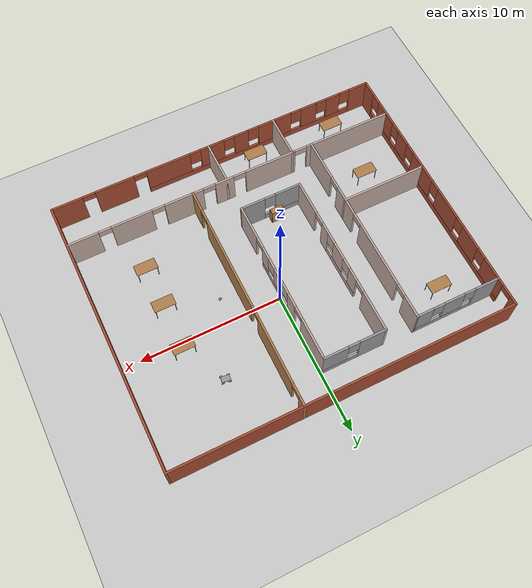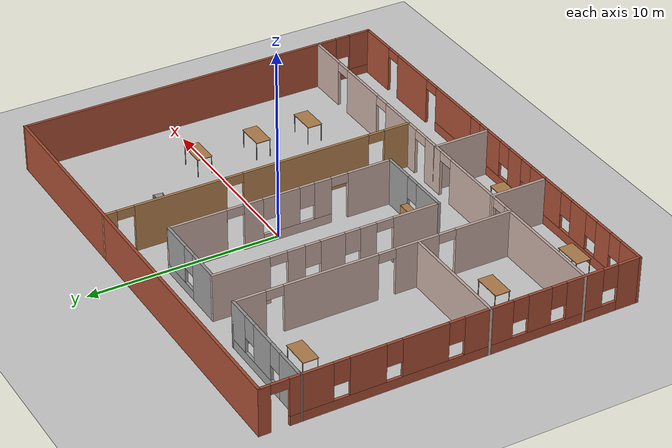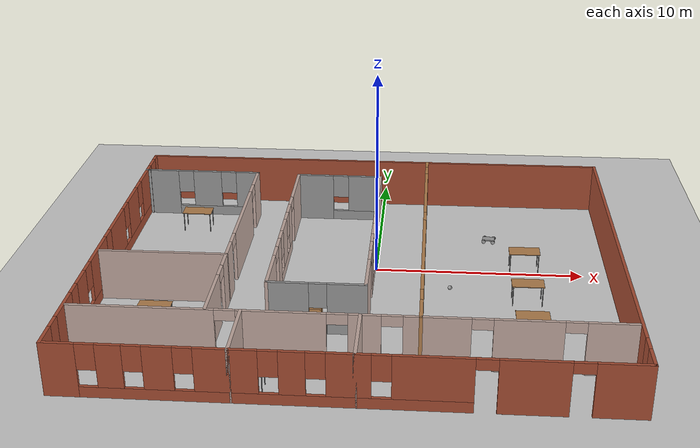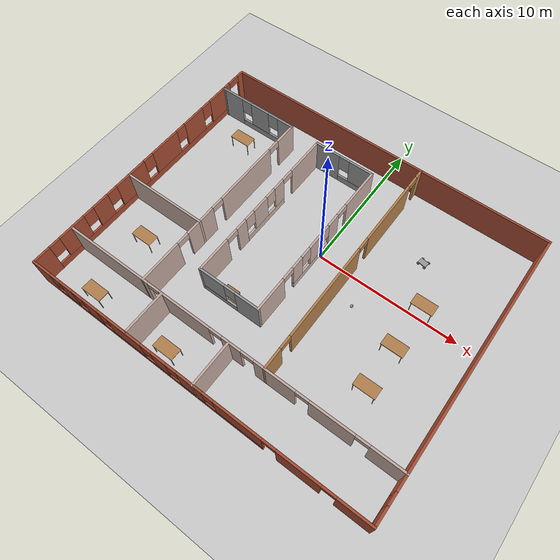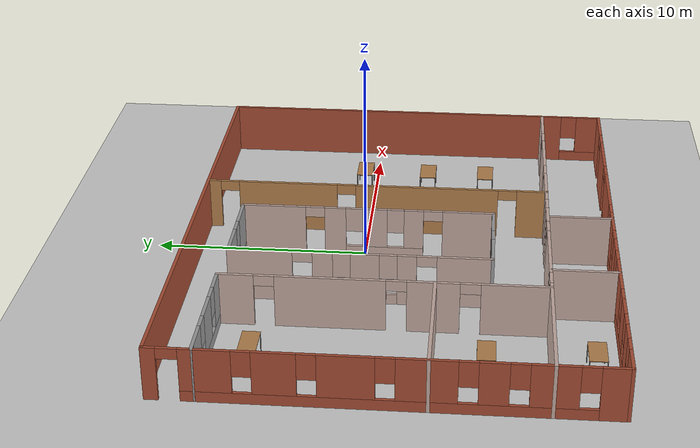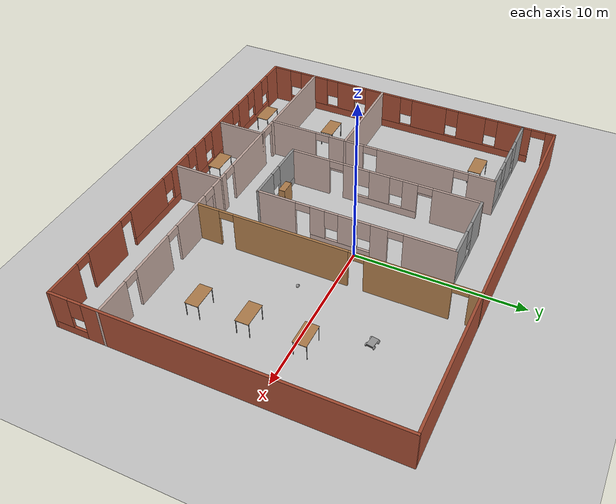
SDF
<sdf version="1.6">
 <world name="default">
  <plugin name="welcome_message" filename="libwelcome_message.so"/>
  <light name="sun" type="directional">
   <pose>0 0 10 0 -0 0</pose>
   <diffuse>0.8 0.8 0.8 1</diffuse>
   <specular>0.2 0.2 0.2 1</specular>
   <attenuation>
    <range>1000</range>
    <constant>0.9</constant>
    <linear>0.01</linear>
    <quadratic>0.001</quadratic>
   </attenuation>
   <direction>-0.5 0.1 -0.9</direction>
  </light>
  <model name="ground_plane">
   <static>1</static>
   <link name="link">
    <collision name="collision">
     <geometry><plane><normal>0 0 1</normal><size>100 100</size></plane></geometry>
     <surface>
      <contact><collide_bitmask>65535</collide_bitmask></contact>
      <friction><ode><mu>100</mu><mu2>50</mu2></ode></friction>
     </surface>
    </collision>
    <visual name="visual">
     <cast_shadows>0</cast_shadows>
     <geometry><plane><normal>0 0 1</normal><size>100 100</size></plane></geometry>
     <material>
      <script><uri>file://media/materials/scripts/gazebo.material</uri><name>Gazebo/Grey</name></script>
     </material>
    </visual>
   </link>
  </model>
  <gravity>0 0 -9.8</gravity>
  <magnetic_field>6e-06 2.3e-05 -4.2e-05</magnetic_field>
  <atmosphere type="adiabatic"/>
  <physics name="default_physics" default="0" type="ode">
   <max_step_size>0.001</max_step_size>
   <real_time_factor>1</real_time_factor>
   <real_time_update_rate>1000</real_time_update_rate>
  </physics>
  <scene><ambient>0.4 0.4 0.4 1</ambient><background>0.7 0.7 0.7 1</background><shadows>1</shadows></scene>
  <spherical_coordinates>
   <surface_model>EARTH_WGS84</surface_model>
   <latitude_deg>0</latitude_deg>
   <longitude_deg>0</longitude_deg>
   <elevation>0</elevation>
   <heading_deg>0</heading_deg>
  </spherical_coordinates>
  <model name="Building">
   <pose>-0.7082 -1.8337 0 0 -0 0</pose>
   <link name="Wall_0">
    <pose>-11.9964 0 0 0 -0 1.5708</pose>
    <visual name="Wall_0_Visual_0">
     <pose>-9.18969 0 1.25 0 -0 0</pose>
     <geometry><box><size>1.27061 0.15 2.5</size></box></geometry>
     <material>
      <script><uri>file://media/materials/scripts/gazebo.material</uri><name>Gazebo/Bricks</name></script>
      <ambient>0.760784 0.662745 0.627451 1</ambient>
     </material>
     <meta><layer>0</layer></meta>
    </visual>
    <collision name="Wall_0_Collision_0">
     <geometry><box><size>1.27061 0.15 2.5</size></box></geometry>
     <pose>-9.18969 0 1.25 0 -0 0</pose>
    </collision>
    <visual name="Wall_0_Visual_1">
     <pose>9.51531 0 1.25 0 -0 0</pose>
     <geometry><box><size>0.619384 0.15 2.5</size></box></geometry>
     <material>
      <script><uri>file://media/materials/scripts/gazebo.material</uri><name>Gazebo/Bricks</name></script>
      <ambient>0.760784 0.662745 0.627451 1</ambient>
     </material>
     <meta><layer>0</layer></meta>
    </visual>
    <collision name="Wall_0_Collision_1">
     <geometry><box><size>0.619384 0.15 2.5</size></box></geometry>
     <pose>9.51531 0 1.25 0 -0 0</pose>
    </collision>
    <visual name="Wall_0_Visual_2">
     <pose>-0.124385 0 0.25 0 -0 0</pose>
     <geometry><box><size>16.86 0.15 0.5</size></box></geometry>
     <material>
      <script><uri>file://media/materials/scripts/gazebo.material</uri><name>Gazebo/Bricks</name></script>
      <ambient>0.760784 0.662745 0.627451 1</ambient>
     </material>
     <meta><layer>0</layer></meta>
    </visual>
    <collision name="Wall_0_Collision_2">
     <geometry><box><size>16.86 0.15 0.5</size></box></geometry>
     <pose>-0.124385 0 0.25 0 -0 0</pose>
    </collision>
    <visual name="Wall_0_Visual_3">
     <pose>-6.76332 0 1.5 0 -0 0</pose>
     <geometry><box><size>1.98213 0.15 2</size></box></geometry>
     <material>
      <script><uri>file://media/materials/scripts/gazebo.material</uri><name>Gazebo/Bricks</name></script>
      <ambient>0.760784 0.662745 0.627451 1</ambient>
     </material>
     <meta><layer>0</layer></meta>
    </visual>
    <collision name="Wall_0_Collision_3">
     <geometry><box><size>1.98213 0.15 2</size></box></geometry>
     <pose>-6.76332 0 1.5 0 -0 0</pose>
    </collision>
    <visual name="Wall_0_Visual_4">
     <pose>-4.35571 0 1.5 0 -0 0</pose>
     <geometry><box><size>1.2331 0.15 2</size></box></geometry>
     <material>
      <script><uri>file://media/materials/scripts/gazebo.material</uri><name>Gazebo/Bricks</name></script>
      <ambient>0.760784 0.662745 0.627451 1</ambient>
     </material>
     <meta><layer>0</layer></meta>
    </visual>
    <collision name="Wall_0_Collision_4">
     <geometry><box><size>1.2331 0.15 2</size></box></geometry>
     <pose>-4.35571 0 1.5 0 -0 0</pose>
    </collision>
    <visual name="Wall_0_Visual_5">
     <pose>-1.68058 0 1.5 0 -0 0</pose>
     <geometry><box><size>2.51715 0.15 2</size></box></geometry>
     <material>
      <script><uri>file://media/materials/scripts/gazebo.material</uri><name>Gazebo/Bricks</name></script>
      <ambient>0.760784 0.662745 0.627451 1</ambient>
     </material>
     <meta><layer>0</layer></meta>
    </visual>
    <collision name="Wall_0_Collision_5">
     <geometry><box><size>2.51715 0.15 2</size></box></geometry>
     <pose>-1.68058 0 1.5 0 -0 0</pose>
    </collision>
    <visual name="Wall_0_Visual_6">
     <pose>1.55632 0 1.5 0 -0 0</pose>
     <geometry><box><size>2.35665 0.15 2</size></box></geometry>
     <material>
      <script><uri>file://media/materials/scripts/gazebo.material</uri><name>Gazebo/Bricks</name></script>
      <ambient>0.760784 0.662745 0.627451 1</ambient>
     </material>
     <meta><layer>0</layer></meta>
    </visual>
    <collision name="Wall_0_Collision_6">
     <geometry><box><size>2.35665 0.15 2</size></box></geometry>
     <pose>1.55632 0 1.5 0 -0 0</pose>
    </collision>
    <visual name="Wall_0_Visual_7">
     <pose>4.44545 0 1.5 0 -0 0</pose>
     <geometry><box><size>1.82162 0.15 2</size></box></geometry>
     <material>
      <script><uri>file://media/materials/scripts/gazebo.material</uri><name>Gazebo/Bricks</name></script>
      <ambient>0.760784 0.662745 0.627451 1</ambient>
     </material>
     <meta><layer>0</layer></meta>
    </visual>
    <collision name="Wall_0_Collision_7">
     <geometry><box><size>1.82162 0.15 2</size></box></geometry>
     <pose>4.44545 0 1.5 0 -0 0</pose>
    </collision>
    <visual name="Wall_0_Visual_8">
     <pose>7.23094 0 1.5 0 -0 0</pose>
     <geometry><box><size>2.14935 0.15 2</size></box></geometry>
     <material>
      <script><uri>file://media/materials/scripts/gazebo.material</uri><name>Gazebo/Bricks</name></script>
      <ambient>0.760784 0.662745 0.627451 1</ambient>
     </material>
     <meta><layer>0</layer></meta>
    </visual>
    <collision name="Wall_0_Collision_8">
     <geometry><box><size>2.14935 0.15 2</size></box></geometry>
     <pose>7.23094 0 1.5 0 -0 0</pose>
    </collision>
    <visual name="Wall_0_Visual_9">
     <pose>-8.15439 0 1.9 0 -0 0</pose>
     <geometry><box><size>0.8 0.15 1.2</size></box></geometry>
     <material>
      <script><uri>file://media/materials/scripts/gazebo.material</uri><name>Gazebo/Bricks</name></script>
      <ambient>0.760784 0.662745 0.627451 1</ambient>
     </material>
     <meta><layer>0</layer></meta>
    </visual>
    <collision name="Wall_0_Collision_9">
     <geometry><box><size>0.8 0.15 1.2</size></box></geometry>
     <pose>-8.15439 0 1.9 0 -0 0</pose>
    </collision>
    <visual name="Wall_0_Visual_10">
     <pose>-5.37226 0 1.9 0 -0 0</pose>
     <geometry><box><size>0.8 0.15 1.2</size></box></geometry>
     <material>
      <script><uri>file://media/materials/scripts/gazebo.material</uri><name>Gazebo/Bricks</name></script>
      <ambient>0.760784 0.662745 0.627451 1</ambient>
     </material>
     <meta><layer>0</layer></meta>
    </visual>
    <collision name="Wall_0_Collision_10">
     <geometry><box><size>0.8 0.15 1.2</size></box></geometry>
     <pose>-5.37226 0 1.9 0 -0 0</pose>
    </collision>
    <visual name="Wall_0_Visual_11">
     <pose>-3.33916 0 1.9 0 -0 0</pose>
     <geometry><box><size>0.8 0.15 1.2</size></box></geometry>
     <material>
      <script><uri>file://media/materials/scripts/gazebo.material</uri><name>Gazebo/Bricks</name></script>
      <ambient>0.760784 0.662745 0.627451 1</ambient>
     </material>
     <meta><layer>0</layer></meta>
    </visual>
    <collision name="Wall_0_Collision_11">
     <geometry><box><size>0.8 0.15 1.2</size></box></geometry>
     <pose>-3.33916 0 1.9 0 -0 0</pose>
    </collision>
    <visual name="Wall_0_Visual_12">
     <pose>-0.022006 0 1.9 0 -0 0</pose>
     <geometry><box><size>0.8 0.15 1.2</size></box></geometry>
     <material>
      <script><uri>file://media/materials/scripts/gazebo.material</uri><name>Gazebo/Bricks</name></script>
      <ambient>0.760784 0.662745 0.627451 1</ambient>
     </material>
     <meta><layer>0</layer></meta>
    </visual>
    <collision name="Wall_0_Collision_12">
     <geometry><box><size>0.8 0.15 1.2</size></box></geometry>
     <pose>-0.022006 0 1.9 0 -0 0</pose>
    </collision>
    <visual name="Wall_0_Visual_13">
     <pose>3.13464 0 1.9 0 -0 0</pose>
     <geometry><box><size>0.8 0.15 1.2</size></box></geometry>
     <material>
      <script><uri>file://media/materials/scripts/gazebo.material</uri><name>Gazebo/Bricks</name></script>
      <ambient>0.760784 0.662745 0.627451 1</ambient>
     </material>
     <meta><layer>0</layer></meta>
    </visual>
    <collision name="Wall_0_Collision_13">
     <geometry><box><size>0.8 0.15 1.2</size></box></geometry>
     <pose>3.13464 0 1.9 0 -0 0</pose>
    </collision>
    <visual name="Wall_0_Visual_14">
     <pose>5.75626 0 1.9 0 -0 0</pose>
     <geometry><box><size>0.8 0.15 1.2</size></box></geometry>
     <material>
      <script><uri>file://media/materials/scripts/gazebo.material</uri><name>Gazebo/Bricks</name></script>
      <ambient>0.760784 0.662745 0.627451 1</ambient>
     </material>
     <meta><layer>0</layer></meta>
    </visual>
    <collision name="Wall_0_Collision_14">
     <geometry><box><size>0.8 0.15 1.2</size></box></geometry>
     <pose>5.75626 0 1.9 0 -0 0</pose>
    </collision>
    <visual name="Wall_0_Visual_15">
     <pose>8.75562 0 2.25 0 -0 0</pose>
     <geometry><box><size>0.9 0.15 0.5</size></box></geometry>
     <material>
      <script><uri>file://media/materials/scripts/gazebo.material</uri><name>Gazebo/Bricks</name></script>
      <ambient>0.760784 0.662745 0.627451 1</ambient>
     </material>
     <meta><layer>0</layer></meta>
    </visual>
    <collision name="Wall_0_Collision_15">
     <geometry><box><size>0.9 0.15 0.5</size></box></geometry>
     <pose>8.75562 0 2.25 0 -0 0</pose>
    </collision>
   </link>
   <link name="Wall_12">
    <pose>3.00359 1.5 0 0 -0 1.5708</pose>
    <visual name="Wall_12_Visual_0">
     <pose>-7.57545 0 1.25 0 -0 0</pose>
     <geometry><box><size>1.49911 0.15 2.5</size></box></geometry>
     <material>
      <script><uri>file://media/materials/scripts/gazebo.material</uri><name>Gazebo/Wood</name></script>
      <ambient>0.760784 0.662745 0.627451 1</ambient>
     </material>
     <meta><layer>0</layer></meta>
    </visual>
    <collision name="Wall_12_Collision_0">
     <geometry><box><size>1.49911 0.15 2.5</size></box></geometry>
     <pose>-7.57545 0 1.25 0 -0 0</pose>
    </collision>
    <visual name="Wall_12_Visual_1">
     <pose>-2.46788 0 1.25 0 -0 0</pose>
     <geometry><box><size>6.91602 0.15 2.5</size></box></geometry>
     <material>
      <script><uri>file://media/materials/scripts/gazebo.material</uri><name>Gazebo/Wood</name></script>
      <ambient>0.760784 0.662745 0.627451 1</ambient>
     </material>
     <meta><layer>0</layer></meta>
    </visual>
    <collision name="Wall_12_Collision_1">
     <geometry><box><size>6.91602 0.15 2.5</size></box></geometry>
     <pose>-2.46788 0 1.25 0 -0 0</pose>
    </collision>
    <visual name="Wall_12_Visual_2">
     <pose>4.30135 0 1.25 0 -0 0</pose>
     <geometry><box><size>4.82244 0.15 2.5</size></box></geometry>
     <material>
      <script><uri>file://media/materials/scripts/gazebo.material</uri><name>Gazebo/Wood</name></script>
      <ambient>0.760784 0.662745 0.627451 1</ambient>
     </material>
     <meta><layer>0</layer></meta>
    </visual>
    <collision name="Wall_12_Collision_2">
     <geometry><box><size>4.82244 0.15 2.5</size></box></geometry>
     <pose>4.30135 0 1.25 0 -0 0</pose>
    </collision>
    <visual name="Wall_12_Visual_3">
     <pose>7.96878 0 1.25 0 -0 0</pose>
     <geometry><box><size>0.712432 0.15 2.5</size></box></geometry>
     <material>
      <script><uri>file://media/materials/scripts/gazebo.material</uri><name>Gazebo/Wood</name></script>
      <ambient>0.760784 0.662745 0.627451 1</ambient>
     </material>
     <meta><layer>0</layer></meta>
    </visual>
    <collision name="Wall_12_Collision_3">
     <geometry><box><size>0.712432 0.15 2.5</size></box></geometry>
     <pose>7.96878 0 1.25 0 -0 0</pose>
    </collision>
    <visual name="Wall_12_Visual_4">
     <pose>-6.37589 0 2.25 0 -0 0</pose>
     <geometry><box><size>0.9 0.15 0.5</size></box></geometry>
     <material>
      <script><uri>file://media/materials/scripts/gazebo.material</uri><name>Gazebo/Wood</name></script>
      <ambient>0.760784 0.662745 0.627451 1</ambient>
     </material>
     <meta><layer>0</layer></meta>
    </visual>
    <collision name="Wall_12_Collision_4">
     <geometry><box><size>0.9 0.15 0.5</size></box></geometry>
     <pose>-6.37589 0 2.25 0 -0 0</pose>
    </collision>
    <visual name="Wall_12_Visual_5">
     <pose>1.44013 0 2.25 0 -0 0</pose>
     <geometry><box><size>0.9 0.15 0.5</size></box></geometry>
     <material>
      <script><uri>file://media/materials/scripts/gazebo.material</uri><name>Gazebo/Wood</name></script>
      <ambient>0.760784 0.662745 0.627451 1</ambient>
     </material>
     <meta><layer>0</layer></meta>
    </visual>
    <collision name="Wall_12_Collision_5">
     <geometry><box><size>0.9 0.15 0.5</size></box></geometry>
     <pose>1.44013 0 2.25 0 -0 0</pose>
    </collision>
    <visual name="Wall_12_Visual_6">
     <pose>7.16257 0 2.25 0 -0 0</pose>
     <geometry><box><size>0.9 0.15 0.5</size></box></geometry>
     <material>
      <script><uri>file://media/materials/scripts/gazebo.material</uri><name>Gazebo/Wood</name></script>
      <ambient>0.760784 0.662745 0.627451 1</ambient>
     </material>
     <meta><layer>0</layer></meta>
    </visual>
    <collision name="Wall_12_Collision_6">
     <geometry><box><size>0.9 0.15 0.5</size></box></geometry>
     <pose>7.16257 0 2.25 0 -0 0</pose>
    </collision>
   </link>
   <link name="Wall_14">
    <collision name="Wall_14_Collision">
     <geometry><box><size>3.15 0.15 2.5</size></box></geometry>
     <pose>0 0 1.25 0 -0 0</pose>
    </collision>
    <visual name="Wall_14_Visual">
     <pose>0 0 1.25 0 -0 0</pose>
     <geometry><box><size>3.15 0.15 2.5</size></box></geometry>
     <material>
      <script><uri>file://media/materials/scripts/gazebo.material</uri><name>Gazebo/Grey</name></script>
      <ambient>0.760784 0.662745 0.627451 1</ambient>
     </material>
     <meta><layer>0</layer></meta>
    </visual>
    <pose>-4.49641 -8.25 0 0 -0 1.5708</pose>
   </link>
   <link name="Wall_16">
    <collision name="Wall_16_Collision">
     <geometry><box><size>3.15 0.15 2.5</size></box></geometry>
     <pose>0 0 1.25 0 -0 0</pose>
    </collision>
    <visual name="Wall_16_Visual">
     <pose>0 0 1.25 0 -0 0</pose>
     <geometry><box><size>3.15 0.15 2.5</size></box></geometry>
     <material>
      <script><uri>file://media/materials/scripts/gazebo.material</uri><name>Gazebo/Grey</name></script>
      <ambient>0.760784 0.662745 0.627451 1</ambient>
     </material>
     <meta><layer>0</layer></meta>
    </visual>
    <pose>0.50359 -8.25 0 0 -0 1.5708</pose>
   </link>
   <link name="Wall_18">
    <pose>-5.99641 0.5 0 0 0 -1.5708</pose>
    <visual name="Wall_18_Visual_0">
     <pose>-6.48888 0 1.25 0 -0 0</pose>
     <geometry><box><size>1.67224 0.15 2.5</size></box></geometry>
     <material>
      <script><uri>file://media/materials/scripts/gazebo.material</uri><name>Gazebo/Grey</name></script>
      <ambient>0.760784 0.662745 0.627451 1</ambient>
     </material>
     <meta><layer>0</layer></meta>
    </visual>
    <collision name="Wall_18_Collision_0">
     <geometry><box><size>1.67224 0.15 2.5</size></box></geometry>
     <pose>-6.48888 0 1.25 0 -0 0</pose>
    </collision>
    <visual name="Wall_18_Visual_1">
     <pose>-2.31363 0 1.25 0 -0 0</pose>
     <geometry><box><size>4.87827 0.15 2.5</size></box></geometry>
     <material>
      <script><uri>file://media/materials/scripts/gazebo.material</uri><name>Gazebo/Grey</name></script>
      <ambient>0.760784 0.662745 0.627451 1</ambient>
     </material>
     <meta><layer>0</layer></meta>
    </visual>
    <collision name="Wall_18_Collision_1">
     <geometry><box><size>4.87827 0.15 2.5</size></box></geometry>
     <pose>-2.31363 0 1.25 0 -0 0</pose>
    </collision>
    <visual name="Wall_18_Visual_2">
     <pose>2.18058 0 1.25 0 -0 0</pose>
     <geometry><box><size>2.31015 0.15 2.5</size></box></geometry>
     <material>
      <script><uri>file://media/materials/scripts/gazebo.material</uri><name>Gazebo/Grey</name></script>
      <ambient>0.760784 0.662745 0.627451 1</ambient>
     </material>
     <meta><layer>0</layer></meta>
    </visual>
    <collision name="Wall_18_Collision_2">
     <geometry><box><size>2.31015 0.15 2.5</size></box></geometry>
     <pose>2.18058 0 1.25 0 -0 0</pose>
    </collision>
    <visual name="Wall_18_Visual_3">
     <pose>5.78033 0 1.25 0 -0 0</pose>
     <geometry><box><size>3.08934 0.15 2.5</size></box></geometry>
     <material>
      <script><uri>file://media/materials/scripts/gazebo.material</uri><name>Gazebo/Grey</name></script>
      <ambient>0.760784 0.662745 0.627451 1</ambient>
     </material>
     <meta><layer>0</layer></meta>
    </visual>
    <collision name="Wall_18_Collision_3">
     <geometry><box><size>3.08934 0.15 2.5</size></box></geometry>
     <pose>5.78033 0 1.25 0 -0 0</pose>
    </collision>
    <visual name="Wall_18_Visual_4">
     <pose>-5.20276 0 2.25 0 -0 0</pose>
     <geometry><box><size>0.9 0.15 0.5</size></box></geometry>
     <material>
      <script><uri>file://media/materials/scripts/gazebo.material</uri><name>Gazebo/Grey</name></script>
      <ambient>0.760784 0.662745 0.627451 1</ambient>
     </material>
     <meta><layer>0</layer></meta>
    </visual>
    <collision name="Wall_18_Collision_4">
     <geometry><box><size>0.9 0.15 0.5</size></box></geometry>
     <pose>-5.20276 0 2.25 0 -0 0</pose>
    </collision>
    <visual name="Wall_18_Visual_5">
     <pose>0.575509 0 2.25 0 -0 0</pose>
     <geometry><box><size>0.9 0.15 0.5</size></box></geometry>
     <material>
      <script><uri>file://media/materials/scripts/gazebo.material</uri><name>Gazebo/Grey</name></script>
      <ambient>0.760784 0.662745 0.627451 1</ambient>
     </material>
     <meta><layer>0</layer></meta>
    </visual>
    <collision name="Wall_18_Collision_5">
     <geometry><box><size>0.9 0.15 0.5</size></box></geometry>
     <pose>0.575509 0 2.25 0 -0 0</pose>
    </collision>
    <visual name="Wall_18_Visual_6">
     <pose>3.78566 0 2.25 0 -0 0</pose>
     <geometry><box><size>0.9 0.15 0.5</size></box></geometry>
     <material>
      <script><uri>file://media/materials/scripts/gazebo.material</uri><name>Gazebo/Grey</name></script>
      <ambient>0.760784 0.662745 0.627451 1</ambient>
     </material>
     <meta><layer>0</layer></meta>
    </visual>
    <collision name="Wall_18_Collision_6">
     <geometry><box><size>0.9 0.15 0.5</size></box></geometry>
     <pose>3.78566 0 2.25 0 -0 0</pose>
    </collision>
   </link>
   <link name="Wall_2">
    <collision name="Wall_2_Collision">
     <geometry><box><size>24.15 0.15 2.5</size></box></geometry>
     <pose>0 0 1.25 0 -0 0</pose>
    </collision>
    <visual name="Wall_2_Visual">
     <pose>0 0 1.25 0 -0 0</pose>
     <geometry><box><size>24.15 0.15 2.5</size></box></geometry>
     <material>
      <script><uri>file://media/materials/scripts/gazebo.material</uri><name>Gazebo/Bricks</name></script>
      <ambient>0.760784 0.662745 0.627451 1</ambient>
     </material>
     <meta><layer>0</layer></meta>
    </visual>
    <pose>0.00359 9.75 0 0 -0 3.14159</pose>
   </link>
   <link name="Wall_20">
    <collision name="Wall_20_Collision">
     <geometry><box><size>0.29021 0.15 2.5</size></box></geometry>
     <pose>0 0 1.25 0 -0 0</pose>
    </collision>
    <visual name="Wall_20_Visual">
     <pose>0 0 1.25 0 -0 0</pose>
     <geometry><box><size>0.29021 0.15 2.5</size></box></geometry>
     <material>
      <script><uri>file://media/materials/scripts/gazebo.material</uri><name>Gazebo/Grey</name></script>
      <ambient>1 1 1 1</ambient>
     </material>
     <meta><layer>0</layer></meta>
    </visual>
    <pose>-11.9267 7.74293 0 0 -0 3.04054</pose>
   </link>
   <link name="Wall_21">
    <pose>-8.99641 7.75 0 0 -0 0</pose>
    <visual name="Wall_21_Visual_0">
     <pose>-2.17796 0 1.25 0 -0 0</pose>
     <geometry><box><size>1.79409 0.15 2.5</size></box></geometry>
     <material>
      <script><uri>file://media/materials/scripts/gazebo.material</uri><name>Gazebo/Grey</name></script>
      <ambient>1 1 1 1</ambient>
     </material>
     <meta><layer>0</layer></meta>
    </visual>
    <collision name="Wall_21_Collision_0">
     <geometry><box><size>1.79409 0.15 2.5</size></box></geometry>
     <pose>-2.17796 0 1.25 0 -0 0</pose>
    </collision>
    <visual name="Wall_21_Visual_1">
     <pose>0.897044 0 0.25 0 -0 0</pose>
     <geometry><box><size>4.35591 0.15 0.5</size></box></geometry>
     <material>
      <script><uri>file://media/materials/scripts/gazebo.material</uri><name>Gazebo/Grey</name></script>
      <ambient>1 1 1 1</ambient>
     </material>
     <meta><layer>0</layer></meta>
    </visual>
    <collision name="Wall_21_Collision_1">
     <geometry><box><size>4.35591 0.15 0.5</size></box></geometry>
     <pose>0.897044 0 0.25 0 -0 0</pose>
    </collision>
    <visual name="Wall_21_Visual_2">
     <pose>0.269391 0 1.5 0 -0 0</pose>
     <geometry><box><size>1.50061 0.15 2</size></box></geometry>
     <material>
      <script><uri>file://media/materials/scripts/gazebo.material</uri><name>Gazebo/Grey</name></script>
      <ambient>1 1 1 1</ambient>
     </material>
     <meta><layer>0</layer></meta>
    </visual>
    <collision name="Wall_21_Collision_2">
     <geometry><box><size>1.50061 0.15 2</size></box></geometry>
     <pose>0.269391 0 1.5 0 -0 0</pose>
    </collision>
    <visual name="Wall_21_Visual_3">
     <pose>2.44735 0 1.5 0 -0 0</pose>
     <geometry><box><size>1.2553 0.15 2</size></box></geometry>
     <material>
      <script><uri>file://media/materials/scripts/gazebo.material</uri><name>Gazebo/Grey</name></script>
      <ambient>1 1 1 1</ambient>
     </material>
     <meta><layer>0</layer></meta>
    </visual>
    <collision name="Wall_21_Collision_3">
     <geometry><box><size>1.2553 0.15 2</size></box></geometry>
     <pose>2.44735 0 1.5 0 -0 0</pose>
    </collision>
    <visual name="Wall_21_Visual_4">
     <pose>-0.880913 0 1.9 0 -0 0</pose>
     <geometry><box><size>0.8 0.15 1.2</size></box></geometry>
     <material>
      <script><uri>file://media/materials/scripts/gazebo.material</uri><name>Gazebo/Grey</name></script>
      <ambient>1 1 1 1</ambient>
     </material>
     <meta><layer>0</layer></meta>
    </visual>
    <collision name="Wall_21_Collision_4">
     <geometry><box><size>0.8 0.15 1.2</size></box></geometry>
     <pose>-0.880913 0 1.9 0 -0 0</pose>
    </collision>
    <visual name="Wall_21_Visual_5">
     <pose>1.41969 0 1.9 0 -0 0</pose>
     <geometry><box><size>0.8 0.15 1.2</size></box></geometry>
     <material>
      <script><uri>file://media/materials/scripts/gazebo.material</uri><name>Gazebo/Grey</name></script>
      <ambient>1 1 1 1</ambient>
     </material>
     <meta><layer>0</layer></meta>
    </visual>
    <collision name="Wall_21_Collision_5">
     <geometry><box><size>0.8 0.15 1.2</size></box></geometry>
     <pose>1.41969 0 1.9 0 -0 0</pose>
    </collision>
   </link>
   <link name="Wall_23">
    <collision name="Wall_23_Collision">
     <geometry><box><size>6.15 0.15 2.5</size></box></geometry>
     <pose>0 0 1.25 0 -0 0</pose>
    </collision>
    <visual name="Wall_23_Visual">
     <pose>0 0 1.25 0 -0 0</pose>
     <geometry><box><size>6.15 0.15 2.5</size></box></geometry>
     <material>
      <script><uri>file://media/materials/scripts/gazebo.material</uri><name>Gazebo/Grey</name></script>
      <ambient>0.760784 0.662745 0.627451 1</ambient>
     </material>
     <meta><layer>0</layer></meta>
    </visual>
    <pose>-8.99641 -1.75 0 0 -0 0</pose>
   </link>
   <link name="Wall_25">
    <pose>-1.60304 7.62885 0 0 -0 0</pose>
    <visual name="Wall_25_Visual_0">
     <pose>-1.28892 0 1.25 0 -0 0</pose>
     <geometry><box><size>1.92216 0.15 2.5</size></box></geometry>
     <material>
      <script><uri>file://media/materials/scripts/gazebo.material</uri><name>Gazebo/Grey</name></script>
      <ambient>1 1 1 1</ambient>
     </material>
     <meta><layer>0</layer></meta>
    </visual>
    <collision name="Wall_25_Collision_0">
     <geometry><box><size>1.92216 0.15 2.5</size></box></geometry>
     <pose>-1.28892 0 1.25 0 -0 0</pose>
    </collision>
    <visual name="Wall_25_Visual_1">
     <pose>0.961079 0 0.25 0 -0 0</pose>
     <geometry><box><size>2.57784 0.15 0.5</size></box></geometry>
     <material>
      <script><uri>file://media/materials/scripts/gazebo.material</uri><name>Gazebo/Grey</name></script>
      <ambient>1 1 1 1</ambient>
     </material>
     <meta><layer>0</layer></meta>
    </visual>
    <collision name="Wall_25_Collision_1">
     <geometry><box><size>2.57784 0.15 0.5</size></box></geometry>
     <pose>0.961079 0 0.25 0 -0 0</pose>
    </collision>
    <visual name="Wall_25_Visual_2">
     <pose>1.36108 0 1.5 0 -0 0</pose>
     <geometry><box><size>1.77784 0.15 2</size></box></geometry>
     <material>
      <script><uri>file://media/materials/scripts/gazebo.material</uri><name>Gazebo/Grey</name></script>
      <ambient>1 1 1 1</ambient>
     </material>
     <meta><layer>0</layer></meta>
    </visual>
    <collision name="Wall_25_Collision_2">
     <geometry><box><size>1.77784 0.15 2</size></box></geometry>
     <pose>1.36108 0 1.5 0 -0 0</pose>
    </collision>
    <visual name="Wall_25_Visual_3">
     <pose>0.072158 0 1.9 0 -0 0</pose>
     <geometry><box><size>0.8 0.15 1.2</size></box></geometry>
     <material>
      <script><uri>file://media/materials/scripts/gazebo.material</uri><name>Gazebo/Grey</name></script>
      <ambient>1 1 1 1</ambient>
     </material>
     <meta><layer>0</layer></meta>
    </visual>
    <collision name="Wall_25_Collision_3">
     <geometry><box><size>0.8 0.15 1.2</size></box></geometry>
     <pose>0.072158 0 1.9 0 -0 0</pose>
    </collision>
   </link>
   <link name="Wall_26">
    <pose>0.571963 1.70385 0 0 0 -1.5708</pose>
    <visual name="Wall_26_Visual_0">
     <pose>-4.47121 0 1.25 0 -0 0</pose>
     <geometry><box><size>3.05758 0.15 2.5</size></box></geometry>
     <material>
      <script><uri>file://media/materials/scripts/gazebo.material</uri><name>Gazebo/Grey</name></script>
      <ambient>0.760784 0.662745 0.627451 1</ambient>
     </material>
     <meta><layer>0</layer></meta>
    </visual>
    <collision name="Wall_26_Collision_0">
     <geometry><box><size>3.05758 0.15 2.5</size></box></geometry>
     <pose>-4.47121 0 1.25 0 -0 0</pose>
    </collision>
    <visual name="Wall_26_Visual_1">
     <pose>-1.53694 0 1.25 0 -0 0</pose>
     <geometry><box><size>1.01096 0.15 2.5</size></box></geometry>
     <material>
      <script><uri>file://media/materials/scripts/gazebo.material</uri><name>Gazebo/Grey</name></script>
      <ambient>0.760784 0.662745 0.627451 1</ambient>
     </material>
     <meta><layer>0</layer></meta>
    </visual>
    <collision name="Wall_26_Collision_1">
     <geometry><box><size>1.01096 0.15 2.5</size></box></geometry>
     <pose>-1.53694 0 1.25 0 -0 0</pose>
    </collision>
    <visual name="Wall_26_Visual_2">
     <pose>4.77022 0 1.25 0 -0 0</pose>
     <geometry><box><size>2.45955 0.15 2.5</size></box></geometry>
     <material>
      <script><uri>file://media/materials/scripts/gazebo.material</uri><name>Gazebo/Grey</name></script>
      <ambient>0.760784 0.662745 0.627451 1</ambient>
     </material>
     <meta><layer>0</layer></meta>
    </visual>
    <collision name="Wall_26_Collision_2">
     <geometry><box><size>2.45955 0.15 2.5</size></box></geometry>
     <pose>4.77022 0 1.25 0 -0 0</pose>
    </collision>
    <visual name="Wall_26_Visual_3">
     <pose>0.804492 0 0.25 0 -0 0</pose>
     <geometry><box><size>3.67191 0.15 0.5</size></box></geometry>
     <material>
      <script><uri>file://media/materials/scripts/gazebo.material</uri><name>Gazebo/Grey</name></script>
      <ambient>0.760784 0.662745 0.627451 1</ambient>
     </material>
     <meta><layer>0</layer></meta>
    </visual>
    <collision name="Wall_26_Collision_3">
     <geometry><box><size>3.67191 0.15 0.5</size></box></geometry>
     <pose>0.804492 0 0.25 0 -0 0</pose>
    </collision>
    <visual name="Wall_26_Visual_4">
     <pose>0.345537 0 1.5 0 -0 0</pose>
     <geometry><box><size>1.154 0.15 2</size></box></geometry>
     <material>
      <script><uri>file://media/materials/scripts/gazebo.material</uri><name>Gazebo/Grey</name></script>
      <ambient>0.760784 0.662745 0.627451 1</ambient>
     </material>
     <meta><layer>0</layer></meta>
    </visual>
    <collision name="Wall_26_Collision_4">
     <geometry><box><size>1.154 0.15 2</size></box></geometry>
     <pose>0.345537 0 1.5 0 -0 0</pose>
    </collision>
    <visual name="Wall_26_Visual_5">
     <pose>2.18149 0 1.5 0 -0 0</pose>
     <geometry><box><size>0.917909 0.15 2</size></box></geometry>
     <material>
      <script><uri>file://media/materials/scripts/gazebo.material</uri><name>Gazebo/Grey</name></script>
      <ambient>0.760784 0.662745 0.627451 1</ambient>
     </material>
     <meta><layer>0</layer></meta>
    </visual>
    <collision name="Wall_26_Collision_5">
     <geometry><box><size>0.917909 0.15 2</size></box></geometry>
     <pose>2.18149 0 1.5 0 -0 0</pose>
    </collision>
    <visual name="Wall_26_Visual_6">
     <pose>-0.631465 0 1.9 0 -0 0</pose>
     <geometry><box><size>0.8 0.15 1.2</size></box></geometry>
     <material>
      <script><uri>file://media/materials/scripts/gazebo.material</uri><name>Gazebo/Grey</name></script>
      <ambient>0.760784 0.662745 0.627451 1</ambient>
     </material>
     <meta><layer>0</layer></meta>
    </visual>
    <collision name="Wall_26_Collision_6">
     <geometry><box><size>0.8 0.15 1.2</size></box></geometry>
     <pose>-0.631465 0 1.9 0 -0 0</pose>
    </collision>
    <visual name="Wall_26_Visual_7">
     <pose>1.32254 0 1.9 0 -0 0</pose>
     <geometry><box><size>0.8 0.15 1.2</size></box></geometry>
     <material>
      <script><uri>file://media/materials/scripts/gazebo.material</uri><name>Gazebo/Grey</name></script>
      <ambient>0.760784 0.662745 0.627451 1</ambient>
     </material>
     <meta><layer>0</layer></meta>
    </visual>
    <collision name="Wall_26_Collision_7">
     <geometry><box><size>0.8 0.15 1.2</size></box></geometry>
     <pose>1.32254 0 1.9 0 -0 0</pose>
    </collision>
    <visual name="Wall_26_Visual_8">
     <pose>-2.49242 0 2.25 0 -0 0</pose>
     <geometry><box><size>0.9 0.15 0.5</size></box></geometry>
     <material>
      <script><uri>file://media/materials/scripts/gazebo.material</uri><name>Gazebo/Grey</name></script>
      <ambient>0.760784 0.662745 0.627451 1</ambient>
     </material>
     <meta><layer>0</layer></meta>
    </visual>
    <collision name="Wall_26_Collision_8">
     <geometry><box><size>0.9 0.15 0.5</size></box></geometry>
     <pose>-2.49242 0 2.25 0 -0 0</pose>
    </collision>
    <visual name="Wall_26_Visual_9">
     <pose>3.09045 0 2.25 0 -0 0</pose>
     <geometry><box><size>0.9 0.15 0.5</size></box></geometry>
     <material>
      <script><uri>file://media/materials/scripts/gazebo.material</uri><name>Gazebo/Grey</name></script>
      <ambient>0.760784 0.662745 0.627451 1</ambient>
     </material>
     <meta><layer>0</layer></meta>
    </visual>
    <collision name="Wall_26_Collision_9">
     <geometry><box><size>0.9 0.15 0.5</size></box></geometry>
     <pose>3.09045 0 2.25 0 -0 0</pose>
    </collision>
   </link>
   <link name="Wall_27">
    <pose>-1.60304 -4.22115 0 0 -0 3.14159</pose>
    <visual name="Wall_27_Visual_0">
     <pose>-1.36108 0 1.25 0 -0 0</pose>
     <geometry><box><size>1.77784 0.15 2.5</size></box></geometry>
     <material>
      <script><uri>file://media/materials/scripts/gazebo.material</uri><name>Gazebo/Grey</name></script>
      <ambient>1 1 1 1</ambient>
     </material>
     <meta><layer>0</layer></meta>
    </visual>
    <collision name="Wall_27_Collision_0">
     <geometry><box><size>1.77784 0.15 2.5</size></box></geometry>
     <pose>-1.36108 0 1.25 0 -0 0</pose>
    </collision>
    <visual name="Wall_27_Visual_1">
     <pose>0.888921 0 0.25 0 -0 0</pose>
     <geometry><box><size>2.72216 0.15 0.5</size></box></geometry>
     <material>
      <script><uri>file://media/materials/scripts/gazebo.material</uri><name>Gazebo/Grey</name></script>
      <ambient>1 1 1 1</ambient>
     </material>
     <meta><layer>0</layer></meta>
    </visual>
    <collision name="Wall_27_Collision_1">
     <geometry><box><size>2.72216 0.15 0.5</size></box></geometry>
     <pose>0.888921 0 0.25 0 -0 0</pose>
    </collision>
    <visual name="Wall_27_Visual_2">
     <pose>1.28892 0 1.5 0 -0 0</pose>
     <geometry><box><size>1.92216 0.15 2</size></box></geometry>
     <material>
      <script><uri>file://media/materials/scripts/gazebo.material</uri><name>Gazebo/Grey</name></script>
      <ambient>1 1 1 1</ambient>
     </material>
     <meta><layer>0</layer></meta>
    </visual>
    <collision name="Wall_27_Collision_2">
     <geometry><box><size>1.92216 0.15 2</size></box></geometry>
     <pose>1.28892 0 1.5 0 -0 0</pose>
    </collision>
    <visual name="Wall_27_Visual_3">
     <pose>-0.072158 0 1.9 0 -0 0</pose>
     <geometry><box><size>0.8 0.15 1.2</size></box></geometry>
     <material>
      <script><uri>file://media/materials/scripts/gazebo.material</uri><name>Gazebo/Grey</name></script>
      <ambient>1 1 1 1</ambient>
     </material>
     <meta><layer>0</layer></meta>
    </visual>
    <collision name="Wall_27_Collision_3">
     <geometry><box><size>0.8 0.15 1.2</size></box></geometry>
     <pose>-0.072158 0 1.9 0 -0 0</pose>
    </collision>
   </link>
   <link name="Wall_28">
    <pose>-3.77804 1.70385 0 0 -0 1.5708</pose>
    <visual name="Wall_28_Visual_0">
     <pose>-4.7237 0 1.25 0 -0 0</pose>
     <geometry><box><size>2.5526 0.15 2.5</size></box></geometry>
     <material>
      <script><uri>file://media/materials/scripts/gazebo.material</uri><name>Gazebo/Grey</name></script>
      <ambient>0.760784 0.662745 0.627451 1</ambient>
     </material>
     <meta><layer>0</layer></meta>
    </visual>
    <collision name="Wall_28_Collision_0">
     <geometry><box><size>2.5526 0.15 2.5</size></box></geometry>
     <pose>-4.7237 0 1.25 0 -0 0</pose>
    </collision>
    <visual name="Wall_28_Visual_1">
     <pose>-2.11171 0 1.25 0 -0 0</pose>
     <geometry><box><size>0.871385 0.15 2.5</size></box></geometry>
     <material>
      <script><uri>file://media/materials/scripts/gazebo.material</uri><name>Gazebo/Grey</name></script>
      <ambient>0.760784 0.662745 0.627451 1</ambient>
     </material>
     <meta><layer>0</layer></meta>
    </visual>
    <collision name="Wall_28_Collision_1">
     <geometry><box><size>0.871385 0.15 2.5</size></box></geometry>
     <pose>-2.11171 0 1.25 0 -0 0</pose>
    </collision>
    <visual name="Wall_28_Visual_2">
     <pose>4.51774 0 1.25 0 -0 0</pose>
     <geometry><box><size>2.96453 0.15 2.5</size></box></geometry>
     <material>
      <script><uri>file://media/materials/scripts/gazebo.material</uri><name>Gazebo/Grey</name></script>
      <ambient>0.760784 0.662745 0.627451 1</ambient>
     </material>
     <meta><layer>0</layer></meta>
    </visual>
    <collision name="Wall_28_Collision_2">
     <geometry><box><size>2.96453 0.15 2.5</size></box></geometry>
     <pose>4.51774 0 1.25 0 -0 0</pose>
    </collision>
    <visual name="Wall_28_Visual_3">
     <pose>0.229727 0 0.25 0 -0 0</pose>
     <geometry><box><size>3.81148 0.15 0.5</size></box></geometry>
     <material>
      <script><uri>file://media/materials/scripts/gazebo.material</uri><name>Gazebo/Grey</name></script>
      <ambient>0.760784 0.662745 0.627451 1</ambient>
     </material>
     <meta><layer>0</layer></meta>
    </visual>
    <collision name="Wall_28_Collision_3">
     <geometry><box><size>3.81148 0.15 0.5</size></box></geometry>
     <pose>0.229727 0 0.25 0 -0 0</pose>
    </collision>
    <visual name="Wall_28_Visual_4">
     <pose>-0.229227 0 1.5 0 -0 0</pose>
     <geometry><box><size>1.29358 0.15 2</size></box></geometry>
     <material>
      <script><uri>file://media/materials/scripts/gazebo.material</uri><name>Gazebo/Grey</name></script>
      <ambient>0.760784 0.662745 0.627451 1</ambient>
     </material>
     <meta><layer>0</layer></meta>
    </visual>
    <collision name="Wall_28_Collision_4">
     <geometry><box><size>1.29358 0.15 2</size></box></geometry>
     <pose>-0.229227 0 1.5 0 -0 0</pose>
    </collision>
    <visual name="Wall_28_Visual_5">
     <pose>1.67651 0 1.5 0 -0 0</pose>
     <geometry><box><size>0.917909 0.15 2</size></box></geometry>
     <material>
      <script><uri>file://media/materials/scripts/gazebo.material</uri><name>Gazebo/Grey</name></script>
      <ambient>0.760784 0.662745 0.627451 1</ambient>
     </material>
     <meta><layer>0</layer></meta>
    </visual>
    <collision name="Wall_28_Collision_5">
     <geometry><box><size>0.917909 0.15 2</size></box></geometry>
     <pose>1.67651 0 1.5 0 -0 0</pose>
    </collision>
    <visual name="Wall_28_Visual_6">
     <pose>-1.27601 0 1.9 0 -0 0</pose>
     <geometry><box><size>0.8 0.15 1.2</size></box></geometry>
     <material>
      <script><uri>file://media/materials/scripts/gazebo.material</uri><name>Gazebo/Grey</name></script>
      <ambient>0.760784 0.662745 0.627451 1</ambient>
     </material>
     <meta><layer>0</layer></meta>
    </visual>
    <collision name="Wall_28_Collision_6">
     <geometry><box><size>0.8 0.15 1.2</size></box></geometry>
     <pose>-1.27601 0 1.9 0 -0 0</pose>
    </collision>
    <visual name="Wall_28_Visual_7">
     <pose>0.817561 0 1.9 0 -0 0</pose>
     <geometry><box><size>0.8 0.15 1.2</size></box></geometry>
     <material>
      <script><uri>file://media/materials/scripts/gazebo.material</uri><name>Gazebo/Grey</name></script>
      <ambient>0.760784 0.662745 0.627451 1</ambient>
     </material>
     <meta><layer>0</layer></meta>
    </visual>
    <collision name="Wall_28_Collision_7">
     <geometry><box><size>0.8 0.15 1.2</size></box></geometry>
     <pose>0.817561 0 1.9 0 -0 0</pose>
    </collision>
    <visual name="Wall_28_Visual_8">
     <pose>-2.9974 0 2.25 0 -0 0</pose>
     <geometry><box><size>0.9 0.15 0.5</size></box></geometry>
     <material>
      <script><uri>file://media/materials/scripts/gazebo.material</uri><name>Gazebo/Grey</name></script>
      <ambient>0.760784 0.662745 0.627451 1</ambient>
     </material>
     <meta><layer>0</layer></meta>
    </visual>
    <collision name="Wall_28_Collision_8">
     <geometry><box><size>0.9 0.15 0.5</size></box></geometry>
     <pose>-2.9974 0 2.25 0 -0 0</pose>
    </collision>
    <visual name="Wall_28_Visual_9">
     <pose>2.58547 0 2.25 0 -0 0</pose>
     <geometry><box><size>0.9 0.15 0.5</size></box></geometry>
     <material>
      <script><uri>file://media/materials/scripts/gazebo.material</uri><name>Gazebo/Grey</name></script>
      <ambient>0.760784 0.662745 0.627451 1</ambient>
     </material>
     <meta><layer>0</layer></meta>
    </visual>
    <collision name="Wall_28_Collision_9">
     <geometry><box><size>0.9 0.15 0.5</size></box></geometry>
     <pose>2.58547 0 2.25 0 -0 0</pose>
    </collision>
   </link>
   <link name="Wall_5">
    <pose>0.00359 -9.75 0 0 -0 0</pose>
    <visual name="Wall_5_Visual_0">
     <pose>-11.3385 0 1.25 0 -0 0</pose>
     <geometry><box><size>1.47307 0.15 2.5</size></box></geometry>
     <material>
      <script><uri>file://media/materials/scripts/gazebo.material</uri><name>Gazebo/Bricks</name></script>
      <ambient>0.760784 0.662745 0.627451 1</ambient>
     </material>
     <meta><layer>0</layer></meta>
    </visual>
    <collision name="Wall_5_Collision_0">
     <geometry><box><size>1.47307 0.15 2.5</size></box></geometry>
     <pose>-11.3385 0 1.25 0 -0 0</pose>
    </collision>
    <visual name="Wall_5_Visual_1">
     <pose>7.49117 0 1.25 0 -0 0</pose>
     <geometry><box><size>2.82191 0.15 2.5</size></box></geometry>
     <material>
      <script><uri>file://media/materials/scripts/gazebo.material</uri><name>Gazebo/Bricks</name></script>
      <ambient>0.760784 0.662745 0.627451 1</ambient>
     </material>
     <meta><layer>0</layer></meta>
    </visual>
    <collision name="Wall_5_Collision_1">
     <geometry><box><size>2.82191 0.15 2.5</size></box></geometry>
     <pose>7.49117 0 1.25 0 -0 0</pose>
    </collision>
    <visual name="Wall_5_Visual_2">
     <pose>10.9386 0 1.25 0 -0 0</pose>
     <geometry><box><size>2.27287 0.15 2.5</size></box></geometry>
     <material>
      <script><uri>file://media/materials/scripts/gazebo.material</uri><name>Gazebo/Bricks</name></script>
      <ambient>0.760784 0.662745 0.627451 1</ambient>
     </material>
     <meta><layer>0</layer></meta>
    </visual>
    <collision name="Wall_5_Collision_2">
     <geometry><box><size>2.27287 0.15 2.5</size></box></geometry>
     <pose>10.9386 0 1.25 0 -0 0</pose>
    </collision>
    <visual name="Wall_5_Visual_3">
     <pose>-2.71086 0 0.25 0 -0 0</pose>
     <geometry><box><size>15.7821 0.15 0.5</size></box></geometry>
     <material>
      <script><uri>file://media/materials/scripts/gazebo.material</uri><name>Gazebo/Bricks</name></script>
      <ambient>0.760784 0.662745 0.627451 1</ambient>
     </material>
     <meta><layer>0</layer></meta>
    </visual>
    <collision name="Wall_5_Collision_3">
     <geometry><box><size>15.7821 0.15 0.5</size></box></geometry>
     <pose>-2.71086 0 0.25 0 -0 0</pose>
    </collision>
    <visual name="Wall_5_Visual_4">
     <pose>-9.26563 0 1.5 0 -0 0</pose>
     <geometry><box><size>1.07259 0.15 2</size></box></geometry>
     <material>
      <script><uri>file://media/materials/scripts/gazebo.material</uri><name>Gazebo/Bricks</name></script>
      <ambient>0.760784 0.662745 0.627451 1</ambient>
     </material>
     <meta><layer>0</layer></meta>
    </visual>
    <collision name="Wall_5_Collision_4">
     <geometry><box><size>1.07259 0.15 2</size></box></geometry>
     <pose>-9.26563 0 1.5 0 -0 0</pose>
    </collision>
    <visual name="Wall_5_Visual_5">
     <pose>-7.31279 0 1.5 0 -0 0</pose>
     <geometry><box><size>1.23309 0.15 2</size></box></geometry>
     <material>
      <script><uri>file://media/materials/scripts/gazebo.material</uri><name>Gazebo/Bricks</name></script>
      <ambient>0.760784 0.662745 0.627451 1</ambient>
     </material>
     <meta><layer>0</layer></meta>
    </visual>
    <collision name="Wall_5_Collision_5">
     <geometry><box><size>1.23309 0.15 2</size></box></geometry>
     <pose>-7.31279 0 1.5 0 -0 0</pose>
    </collision>
    <visual name="Wall_5_Visual_6">
     <pose>-4.61092 0 1.5 0 -0 0</pose>
     <geometry><box><size>2.57066 0.15 2</size></box></geometry>
     <material>
      <script><uri>file://media/materials/scripts/gazebo.material</uri><name>Gazebo/Bricks</name></script>
      <ambient>0.760784 0.662745 0.627451 1</ambient>
     </material>
     <meta><layer>0</layer></meta>
    </visual>
    <collision name="Wall_5_Collision_6">
     <geometry><box><size>2.57066 0.15 2</size></box></geometry>
     <pose>-4.61092 0 1.5 0 -0 0</pose>
    </collision>
    <visual name="Wall_5_Visual_7">
     <pose>-1.98929 0 1.5 0 -0 0</pose>
     <geometry><box><size>1.07259 0.15 2</size></box></geometry>
     <material>
      <script><uri>file://media/materials/scripts/gazebo.material</uri><name>Gazebo/Bricks</name></script>
      <ambient>0.760784 0.662745 0.627451 1</ambient>
     </material>
     <meta><layer>0</layer></meta>
    </visual>
    <collision name="Wall_5_Collision_7">
     <geometry><box><size>1.07259 0.15 2</size></box></geometry>
     <pose>-1.98929 0 1.5 0 -0 0</pose>
    </collision>
    <visual name="Wall_5_Visual_8">
     <pose>0.241555 0 1.5 0 -0 0</pose>
     <geometry><box><size>1.78911 0.15 2</size></box></geometry>
     <material>
      <script><uri>file://media/materials/scripts/gazebo.material</uri><name>Gazebo/Bricks</name></script>
      <ambient>0.760784 0.662745 0.627451 1</ambient>
     </material>
     <meta><layer>0</layer></meta>
    </visual>
    <collision name="Wall_5_Collision_8">
     <geometry><box><size>1.78911 0.15 2</size></box></geometry>
     <pose>0.241555 0 1.5 0 -0 0</pose>
    </collision>
    <visual name="Wall_5_Visual_9">
     <pose>3.55816 0 1.5 0 -0 0</pose>
     <geometry><box><size>3.2441 0.15 2</size></box></geometry>
     <material>
      <script><uri>file://media/materials/scripts/gazebo.material</uri><name>Gazebo/Bricks</name></script>
      <ambient>0.760784 0.662745 0.627451 1</ambient>
     </material>
     <meta><layer>0</layer></meta>
    </visual>
    <collision name="Wall_5_Collision_9">
     <geometry><box><size>3.2441 0.15 2</size></box></geometry>
     <pose>3.55816 0 1.5 0 -0 0</pose>
    </collision>
    <visual name="Wall_5_Visual_10">
     <pose>-10.2019 0 1.9 0 -0 0</pose>
     <geometry><box><size>0.8 0.15 1.2</size></box></geometry>
     <material>
      <script><uri>file://media/materials/scripts/gazebo.material</uri><name>Gazebo/Bricks</name></script>
      <ambient>0.760784 0.662745 0.627451 1</ambient>
     </material>
     <meta><layer>0</layer></meta>
    </visual>
    <collision name="Wall_5_Collision_10">
     <geometry><box><size>0.8 0.15 1.2</size></box></geometry>
     <pose>-10.2019 0 1.9 0 -0 0</pose>
    </collision>
    <visual name="Wall_5_Visual_11">
     <pose>-8.32934 0 1.9 0 -0 0</pose>
     <geometry><box><size>0.8 0.15 1.2</size></box></geometry>
     <material>
      <script><uri>file://media/materials/scripts/gazebo.material</uri><name>Gazebo/Bricks</name></script>
      <ambient>0.760784 0.662745 0.627451 1</ambient>
     </material>
     <meta><layer>0</layer></meta>
    </visual>
    <collision name="Wall_5_Collision_11">
     <geometry><box><size>0.8 0.15 1.2</size></box></geometry>
     <pose>-8.32934 0 1.9 0 -0 0</pose>
    </collision>
    <visual name="Wall_5_Visual_12">
     <pose>-6.29625 0 1.9 0 -0 0</pose>
     <geometry><box><size>0.8 0.15 1.2</size></box></geometry>
     <material>
      <script><uri>file://media/materials/scripts/gazebo.material</uri><name>Gazebo/Bricks</name></script>
      <ambient>0.760784 0.662745 0.627451 1</ambient>
     </material>
     <meta><layer>0</layer></meta>
    </visual>
    <collision name="Wall_5_Collision_12">
     <geometry><box><size>0.8 0.15 1.2</size></box></geometry>
     <pose>-6.29625 0 1.9 0 -0 0</pose>
    </collision>
    <visual name="Wall_5_Visual_13">
     <pose>-2.92559 0 1.9 0 -0 0</pose>
     <geometry><box><size>0.8 0.15 1.2</size></box></geometry>
     <material>
      <script><uri>file://media/materials/scripts/gazebo.material</uri><name>Gazebo/Bricks</name></script>
      <ambient>0.760784 0.662745 0.627451 1</ambient>
     </material>
     <meta><layer>0</layer></meta>
    </visual>
    <collision name="Wall_5_Collision_13">
     <geometry><box><size>0.8 0.15 1.2</size></box></geometry>
     <pose>-2.92559 0 1.9 0 -0 0</pose>
    </collision>
    <visual name="Wall_5_Visual_14">
     <pose>-1.053 0 1.9 0 -0 0</pose>
     <geometry><box><size>0.8 0.15 1.2</size></box></geometry>
     <material>
      <script><uri>file://media/materials/scripts/gazebo.material</uri><name>Gazebo/Bricks</name></script>
      <ambient>0.760784 0.662745 0.627451 1</ambient>
     </material>
     <meta><layer>0</layer></meta>
    </visual>
    <collision name="Wall_5_Collision_14">
     <geometry><box><size>0.8 0.15 1.2</size></box></geometry>
     <pose>-1.053 0 1.9 0 -0 0</pose>
    </collision>
    <visual name="Wall_5_Visual_15">
     <pose>1.53611 0 1.9 0 -0 0</pose>
     <geometry><box><size>0.8 0.15 1.2</size></box></geometry>
     <material>
      <script><uri>file://media/materials/scripts/gazebo.material</uri><name>Gazebo/Bricks</name></script>
      <ambient>0.760784 0.662745 0.627451 1</ambient>
     </material>
     <meta><layer>0</layer></meta>
    </visual>
    <collision name="Wall_5_Collision_15">
     <geometry><box><size>0.8 0.15 1.2</size></box></geometry>
     <pose>1.53611 0 1.9 0 -0 0</pose>
    </collision>
    <visual name="Wall_5_Visual_16">
     <pose>9.35213 0 2.25 0 -0 0</pose>
     <geometry><box><size>0.9 0.15 0.5</size></box></geometry>
     <material>
      <script><uri>file://media/materials/scripts/gazebo.material</uri><name>Gazebo/Bricks</name></script>
      <ambient>0.760784 0.662745 0.627451 1</ambient>
     </material>
     <meta><layer>0</layer></meta>
    </visual>
    <collision name="Wall_5_Collision_16">
     <geometry><box><size>0.9 0.15 0.5</size></box></geometry>
     <pose>9.35213 0 2.25 0 -0 0</pose>
    </collision>
    <visual name="Wall_5_Visual_17">
     <pose>5.63021 0 2.25 0 -0 0</pose>
     <geometry><box><size>0.9 0.15 0.5</size></box></geometry>
     <material>
      <script><uri>file://media/materials/scripts/gazebo.material</uri><name>Gazebo/Bricks</name></script>
      <ambient>0.760784 0.662745 0.627451 1</ambient>
     </material>
     <meta><layer>0</layer></meta>
    </visual>
    <collision name="Wall_5_Collision_17">
     <geometry><box><size>0.9 0.15 0.5</size></box></geometry>
     <pose>5.63021 0 2.25 0 -0 0</pose>
    </collision>
   </link>
   <link name="Wall_7">
    <pose>12.0036 0 0 0 0 -1.5708</pose>
    <visual name="Wall_7_Visual_0">
     <pose>-1.02296 0 1.25 0 -0 0</pose>
     <geometry><box><size>17.6041 0.15 2.5</size></box></geometry>
     <material>
      <script><uri>file://media/materials/scripts/gazebo.material</uri><name>Gazebo/Bricks</name></script>
      <ambient>0.760784 0.662745 0.627451 1</ambient>
     </material>
     <meta><layer>0</layer></meta>
    </visual>
    <collision name="Wall_7_Collision_0">
     <geometry><box><size>17.6041 0.15 2.5</size></box></geometry>
     <pose>-1.02296 0 1.25 0 -0 0</pose>
    </collision>
    <visual name="Wall_7_Visual_1">
     <pose>8.80204 0 0.25 0 -0 0</pose>
     <geometry><box><size>2.04591 0.15 0.5</size></box></geometry>
     <material>
      <script><uri>file://media/materials/scripts/gazebo.material</uri><name>Gazebo/Bricks</name></script>
      <ambient>0.760784 0.662745 0.627451 1</ambient>
     </material>
     <meta><layer>0</layer></meta>
    </visual>
    <collision name="Wall_7_Collision_1">
     <geometry><box><size>2.04591 0.15 0.5</size></box></geometry>
     <pose>8.80204 0 0.25 0 -0 0</pose>
    </collision>
    <visual name="Wall_7_Visual_2">
     <pose>9.20204 0 1.5 0 -0 0</pose>
     <geometry><box><size>1.24591 0.15 2</size></box></geometry>
     <material>
      <script><uri>file://media/materials/scripts/gazebo.material</uri><name>Gazebo/Bricks</name></script>
      <ambient>0.760784 0.662745 0.627451 1</ambient>
     </material>
     <meta><layer>0</layer></meta>
    </visual>
    <collision name="Wall_7_Collision_2">
     <geometry><box><size>1.24591 0.15 2</size></box></geometry>
     <pose>9.20204 0 1.5 0 -0 0</pose>
    </collision>
    <visual name="Wall_7_Visual_3">
     <pose>8.17909 0 1.9 0 -0 0</pose>
     <geometry><box><size>0.8 0.15 1.2</size></box></geometry>
     <material>
      <script><uri>file://media/materials/scripts/gazebo.material</uri><name>Gazebo/Bricks</name></script>
      <ambient>0.760784 0.662745 0.627451 1</ambient>
     </material>
     <meta><layer>0</layer></meta>
    </visual>
    <collision name="Wall_7_Collision_3">
     <geometry><box><size>0.8 0.15 1.2</size></box></geometry>
     <pose>8.17909 0 1.9 0 -0 0</pose>
    </collision>
   </link>
   <link name="Wall_9">
    <pose>0.00359 -6.75 0 0 -0 0</pose>
    <visual name="Wall_9_Visual_0">
     <pose>-8.84417 0 1.25 0 -0 0</pose>
     <geometry><box><size>6.46167 0.15 2.5</size></box></geometry>
     <material>
      <script><uri>file://media/materials/scripts/gazebo.material</uri><name>Gazebo/Grey</name></script>
      <ambient>0.760784 0.662745 0.627451 1</ambient>
     </material>
     <meta><layer>0</layer></meta>
    </visual>
    <collision name="Wall_9_Collision_0">
     <geometry><box><size>6.46167 0.15 2.5</size></box></geometry>
     <pose>-8.84417 0 1.25 0 -0 0</pose>
    </collision>
    <visual name="Wall_9_Visual_1">
     <pose>-2.81388 0 1.25 0 -0 0</pose>
     <geometry><box><size>3.79892 0.15 2.5</size></box></geometry>
     <material>
      <script><uri>file://media/materials/scripts/gazebo.material</uri><name>Gazebo/Grey</name></script>
      <ambient>0.760784 0.662745 0.627451 1</ambient>
     </material>
     <meta><layer>0</layer></meta>
    </visual>
    <collision name="Wall_9_Collision_1">
     <geometry><box><size>3.79892 0.15 2.5</size></box></geometry>
     <pose>-2.81388 0 1.25 0 -0 0</pose>
    </collision>
    <visual name="Wall_9_Visual_2">
     <pose>0.675416 0 1.25 0 -0 0</pose>
     <geometry><box><size>1.37967 0.15 2.5</size></box></geometry>
     <material>
      <script><uri>file://media/materials/scripts/gazebo.material</uri><name>Gazebo/Grey</name></script>
      <ambient>0.760784 0.662745 0.627451 1</ambient>
     </material>
     <meta><layer>0</layer></meta>
    </visual>
    <collision name="Wall_9_Collision_2">
     <geometry><box><size>1.37967 0.15 2.5</size></box></geometry>
     <pose>0.675416 0 1.25 0 -0 0</pose>
    </collision>
    <visual name="Wall_9_Visual_3">
     <pose>3.67621 0 1.25 0 -0 0</pose>
     <geometry><box><size>2.82191 0.15 2.5</size></box></geometry>
     <material>
      <script><uri>file://media/materials/scripts/gazebo.material</uri><name>Gazebo/Grey</name></script>
      <ambient>0.760784 0.662745 0.627451 1</ambient>
     </material>
     <meta><layer>0</layer></meta>
    </visual>
    <collision name="Wall_9_Collision_3">
     <geometry><box><size>2.82191 0.15 2.5</size></box></geometry>
     <pose>3.67621 0 1.25 0 -0 0</pose>
    </collision>
    <visual name="Wall_9_Visual_4">
     <pose>7.44465 0 1.25 0 -0 0</pose>
     <geometry><box><size>2.91496 0.15 2.5</size></box></geometry>
     <material>
      <script><uri>file://media/materials/scripts/gazebo.material</uri><name>Gazebo/Grey</name></script>
      <ambient>0.760784 0.662745 0.627451 1</ambient>
     </material>
     <meta><layer>0</layer></meta>
    </visual>
    <collision name="Wall_9_Collision_4">
     <geometry><box><size>2.91496 0.15 2.5</size></box></geometry>
     <pose>7.44465 0 1.25 0 -0 0</pose>
    </collision>
    <visual name="Wall_9_Visual_5">
     <pose>10.9386 0 1.25 0 -0 0</pose>
     <geometry><box><size>2.27287 0.15 2.5</size></box></geometry>
     <material>
      <script><uri>file://media/materials/scripts/gazebo.material</uri><name>Gazebo/Grey</name></script>
      <ambient>0.760784 0.662745 0.627451 1</ambient>
     </material>
     <meta><layer>0</layer></meta>
    </visual>
    <collision name="Wall_9_Collision_5">
     <geometry><box><size>2.27287 0.15 2.5</size></box></geometry>
     <pose>10.9386 0 1.25 0 -0 0</pose>
    </collision>
    <visual name="Wall_9_Visual_6">
     <pose>-5.16333 0 2.25 0 -0 0</pose>
     <geometry><box><size>0.9 0.15 0.5</size></box></geometry>
     <material>
      <script><uri>file://media/materials/scripts/gazebo.material</uri><name>Gazebo/Grey</name></script>
      <ambient>0.760784 0.662745 0.627451 1</ambient>
     </material>
     <meta><layer>0</layer></meta>
    </visual>
    <collision name="Wall_9_Collision_6">
     <geometry><box><size>0.9 0.15 0.5</size></box></geometry>
     <pose>-5.16333 0 2.25 0 -0 0</pose>
    </collision>
    <visual name="Wall_9_Visual_7">
     <pose>-0.464419 0 2.25 0 -0 0</pose>
     <geometry><box><size>0.9 0.15 0.5</size></box></geometry>
     <material>
      <script><uri>file://media/materials/scripts/gazebo.material</uri><name>Gazebo/Grey</name></script>
      <ambient>0.760784 0.662745 0.627451 1</ambient>
     </material>
     <meta><layer>0</layer></meta>
    </visual>
    <collision name="Wall_9_Collision_7">
     <geometry><box><size>0.9 0.15 0.5</size></box></geometry>
     <pose>-0.464419 0 2.25 0 -0 0</pose>
    </collision>
    <visual name="Wall_9_Visual_8">
     <pose>1.81525 0 2.25 0 -0 0</pose>
     <geometry><box><size>0.9 0.15 0.5</size></box></geometry>
     <material>
      <script><uri>file://media/materials/scripts/gazebo.material</uri><name>Gazebo/Grey</name></script>
      <ambient>0.760784 0.662745 0.627451 1</ambient>
     </material>
     <meta><layer>0</layer></meta>
    </visual>
    <collision name="Wall_9_Collision_8">
     <geometry><box><size>0.9 0.15 0.5</size></box></geometry>
     <pose>1.81525 0 2.25 0 -0 0</pose>
    </collision>
    <visual name="Wall_9_Visual_9">
     <pose>5.53716 0 2.25 0 -0 0</pose>
     <geometry><box><size>0.9 0.15 0.5</size></box></geometry>
     <material>
      <script><uri>file://media/materials/scripts/gazebo.material</uri><name>Gazebo/Grey</name></script>
      <ambient>0.760784 0.662745 0.627451 1</ambient>
     </material>
     <meta><layer>0</layer></meta>
    </visual>
    <collision name="Wall_9_Collision_9">
     <geometry><box><size>0.9 0.15 0.5</size></box></geometry>
     <pose>5.53716 0 2.25 0 -0 0</pose>
    </collision>
    <visual name="Wall_9_Visual_10">
     <pose>9.35213 0 2.25 0 -0 0</pose>
     <geometry><box><size>0.9 0.15 0.5</size></box></geometry>
     <material>
      <script><uri>file://media/materials/scripts/gazebo.material</uri><name>Gazebo/Grey</name></script>
      <ambient>0.760784 0.662745 0.627451 1</ambient>
     </material>
     <meta><layer>0</layer></meta>
    </visual>
    <collision name="Wall_9_Collision_10">
     <geometry><box><size>0.9 0.15 0.5</size></box></geometry>
     <pose>9.35213 0 2.25 0 -0 0</pose>
    </collision>
   </link>
   <static>1</static>
  </model>
  <model name="FourWheeledRobot_0">
   <link name="link_0">
    <pose>-0.26 0 -0.008571 0 -0 0</pose>
    <inertial>
     <mass>1</mass>
     <inertia>
      <ixx>0.166667</ixx>
      <ixy>0</ixy>
      <ixz>0</ixz>
      <iyy>0.166667</iyy>
      <iyz>0</iyz>
      <izz>0.166667</izz>
     </inertia>
    </inertial>
    <visual name="visual">
     <geometry><box><size>0.1 0.4 0.06</size></box></geometry>
     <material>
      <lighting>1</lighting>
      <script><uri>file://media/materials/scripts/gazebo.material</uri><name>Gazebo/Grey</name></script>
      <shader type="pixel"><normal_map>__default__</normal_map></shader>
      <ambient>0.3 0.3 0.3 1</ambient>
      <diffuse>0.7 0.7 0.7 1</diffuse>
      <specular>0.01 0.01 0.01 1</specular>
      <emissive>0 0 0 1</emissive>
     </material>
    </visual>
    <collision name="collision">
     <geometry><box><size>0.1 0.4 0.06</size></box></geometry>
     <surface>
      <friction>
       <ode><mu>1</mu><mu2>1</mu2><fdir1>0 0 0</fdir1><slip1>0</slip1><slip2>0</slip2></ode>
       <torsional>
        <coefficient>1</coefficient>
        <patch_radius>0</patch_radius>
        <surface_radius>0</surface_radius>
        <use_patch_radius>1</use_patch_radius>
        <ode><slip>0</slip></ode>
       </torsional>
      </friction>
      <bounce><restitution_coefficient>0</restitution_coefficient><threshold>1e+06</threshold></bounce>
      <contact>
       <collide_without_contact>0</collide_without_contact>
       <collide_without_contact_bitmask>1</collide_without_contact_bitmask>
       <collide_bitmask>1</collide_bitmask>
       <ode>
        <soft_cfm>0</soft_cfm>
        <soft_erp>0.2</soft_erp>
        <kp>1e+13</kp>
        <kd>1</kd>
        <max_vel>0.01</max_vel>
        <min_depth>0</min_depth>
       </ode>
       <bullet>
        <split_impulse>1</split_impulse>
        <split_impulse_penetration_threshold>-0.01</split_impulse_penetration_threshold>
        <soft_cfm>0</soft_cfm>
        <soft_erp>0.2</soft_erp>
        <kp>1e+13</kp>
        <kd>1</kd>
       </bullet>
      </contact>
     </surface>
    </collision>
   </link>
   <link name="link_0_clone">
    <pose>0.24 0 -0.008571 0 -0 0</pose>
    <inertial>
     <mass>1</mass>
     <inertia>
      <ixx>0.166667</ixx>
      <ixy>0</ixy>
      <ixz>0</ixz>
      <iyy>0.166667</iyy>
      <iyz>0</iyz>
      <izz>0.166667</izz>
     </inertia>
    </inertial>
    <visual name="visual">
     <geometry><box><size>0.1 0.4 0.06</size></box></geometry>
     <material>
      <lighting>1</lighting>
      <script><uri>file://media/materials/scripts/gazebo.material</uri><name>Gazebo/Grey</name></script>
      <shader type="pixel"><normal_map>__default__</normal_map></shader>
      <ambient>0.3 0.3 0.3 1</ambient>
      <diffuse>0.7 0.7 0.7 1</diffuse>
      <specular>0.01 0.01 0.01 1</specular>
      <emissive>0 0 0 1</emissive>
     </material>
    </visual>
    <collision name="collision">
     <geometry><box><size>0.1 0.4 0.06</size></box></geometry>
     <surface>
      <friction>
       <ode><mu>1</mu><mu2>1</mu2><fdir1>0 0 0</fdir1><slip1>0</slip1><slip2>0</slip2></ode>
       <torsional>
        <coefficient>1</coefficient>
        <patch_radius>0</patch_radius>
        <surface_radius>0</surface_radius>
        <use_patch_radius>1</use_patch_radius>
        <ode><slip>0</slip></ode>
       </torsional>
      </friction>
      <bounce><restitution_coefficient>0</restitution_coefficient><threshold>1e+06</threshold></bounce>
      <contact>
       <collide_without_contact>0</collide_without_contact>
       <collide_without_contact_bitmask>1</collide_without_contact_bitmask>
       <collide_bitmask>1</collide_bitmask>
       <ode>
        <soft_cfm>0</soft_cfm>
        <soft_erp>0.2</soft_erp>
        <kp>1e+13</kp>
        <kd>1</kd>
        <max_vel>0.01</max_vel>
        <min_depth>0</min_depth>
       </ode>
       <bullet>
        <split_impulse>1</split_impulse>
        <split_impulse_penetration_threshold>-0.01</split_impulse_penetration_threshold>
        <soft_cfm>0</soft_cfm>
        <soft_erp>0.2</soft_erp>
        <kp>1e+13</kp>
        <kd>1</kd>
       </bullet>
      </contact>
     </surface>
    </collision>
   </link>
   <link name="link_1">
    <pose>-0.01 0 0.051429 0 -0 0</pose>
    <inertial>
     <mass>1</mass>
     <inertia>
      <ixx>0.166667</ixx>
      <ixy>0</ixy>
      <ixz>0</ixz>
      <iyy>0.166667</iyy>
      <iyz>0</iyz>
      <izz>0.166667</izz>
     </inertia>
    </inertial>
    <visual name="visual">
     <geometry><box><size>0.6 0.4 0.06</size></box></geometry>
     <material>
      <lighting>1</lighting>
      <script><uri>file://media/materials/scripts/gazebo.material</uri><name>Gazebo/Grey</name></script>
      <shader type="pixel"><normal_map>__default__</normal_map></shader>
      <ambient>0.3 0.3 0.3 1</ambient>
      <diffuse>0.7 0.7 0.7 1</diffuse>
      <specular>0.01 0.01 0.01 1</specular>
      <emissive>0 0 0 1</emissive>
     </material>
    </visual>
    <collision name="collision">
     <geometry><box><size>0.6 0.4 0.06</size></box></geometry>
     <surface>
      <friction>
       <ode><mu>1</mu><mu2>1</mu2><fdir1>0 0 0</fdir1><slip1>0</slip1><slip2>0</slip2></ode>
       <torsional>
        <coefficient>1</coefficient>
        <patch_radius>0</patch_radius>
        <surface_radius>0</surface_radius>
        <use_patch_radius>1</use_patch_radius>
        <ode><slip>0</slip></ode>
       </torsional>
      </friction>
      <bounce><restitution_coefficient>0</restitution_coefficient><threshold>1e+06</threshold></bounce>
      <contact>
       <collide_without_contact>0</collide_without_contact>
       <collide_without_contact_bitmask>1</collide_without_contact_bitmask>
       <collide_bitmask>1</collide_bitmask>
       <ode>
        <soft_cfm>0</soft_cfm>
        <soft_erp>0.2</soft_erp>
        <kp>1e+13</kp>
        <kd>1</kd>
        <max_vel>0.01</max_vel>
        <min_depth>0</min_depth>
       </ode>
       <bullet>
        <split_impulse>1</split_impulse>
        <split_impulse_penetration_threshold>-0.01</split_impulse_penetration_threshold>
        <soft_cfm>0</soft_cfm>
        <soft_erp>0.2</soft_erp>
        <kp>1e+13</kp>
        <kd>1</kd>
       </bullet>
      </contact>
     </surface>
    </collision>
   </link>
   <link name="link_2">
    <pose>-0.235 -0.230013 -0.008571 1.5707 -0 0</pose>
    <inertial>
     <mass>1</mass>
     <inertia><ixx>0.145833</ixx><ixy>0</ixy><ixz>0</ixz><iyy>0.145833</iyy><iyz>0</iyz><izz>0.125</izz></inertia>
    </inertial>
    <visual name="visual">
     <geometry><cylinder><radius>0.1</radius><length>0.06</length></cylinder></geometry>
     <material>
      <lighting>1</lighting>
      <script><uri>file://media/materials/scripts/gazebo.material</uri><name>Gazebo/Grey</name></script>
      <shader type="pixel"><normal_map>__default__</normal_map></shader>
      <ambient>0.3 0.3 0.3 1</ambient>
      <diffuse>0.7 0.7 0.7 1</diffuse>
      <specular>0.01 0.01 0.01 1</specular>
      <emissive>0 0 0 1</emissive>
     </material>
    </visual>
    <collision name="collision">
     <geometry><cylinder><radius>0.1</radius><length>0.06</length></cylinder></geometry>
     <surface>
      <friction>
       <ode><mu>1</mu><mu2>1</mu2><fdir1>0 0 0</fdir1><slip1>0</slip1><slip2>0</slip2></ode>
       <torsional>
        <coefficient>1</coefficient>
        <patch_radius>0</patch_radius>
        <surface_radius>0</surface_radius>
        <use_patch_radius>1</use_patch_radius>
        <ode><slip>0</slip></ode>
       </torsional>
      </friction>
      <bounce><restitution_coefficient>0</restitution_coefficient><threshold>1e+06</threshold></bounce>
      <contact>
       <collide_without_contact>0</collide_without_contact>
       <collide_without_contact_bitmask>1</collide_without_contact_bitmask>
       <collide_bitmask>1</collide_bitmask>
       <ode>
        <soft_cfm>0</soft_cfm>
        <soft_erp>0.2</soft_erp>
        <kp>1e+13</kp>
        <kd>1</kd>
        <max_vel>0.01</max_vel>
        <min_depth>0</min_depth>
       </ode>
       <bullet>
        <split_impulse>1</split_impulse>
        <split_impulse_penetration_threshold>-0.01</split_impulse_penetration_threshold>
        <soft_cfm>0</soft_cfm>
        <soft_erp>0.2</soft_erp>
        <kp>1e+13</kp>
        <kd>1</kd>
       </bullet>
      </contact>
     </surface>
    </collision>
   </link>
   <link name="link_2_clone">
    <pose>-0.215 0.23001 -0.008571 1.5707 -0 0</pose>
    <inertial>
     <mass>1</mass>
     <inertia><ixx>0.145833</ixx><ixy>0</ixy><ixz>0</ixz><iyy>0.145833</iyy><iyz>0</iyz><izz>0.125</izz></inertia>
    </inertial>
    <visual name="visual">
     <geometry><cylinder><radius>0.1</radius><length>0.06</length></cylinder></geometry>
     <material>
      <lighting>1</lighting>
      <script><uri>file://media/materials/scripts/gazebo.material</uri><name>Gazebo/Grey</name></script>
      <shader type="pixel"><normal_map>__default__</normal_map></shader>
      <ambient>0.3 0.3 0.3 1</ambient>
      <diffuse>0.7 0.7 0.7 1</diffuse>
      <specular>0.01 0.01 0.01 1</specular>
      <emissive>0 0 0 1</emissive>
     </material>
    </visual>
    <collision name="collision">
     <geometry><cylinder><radius>0.1</radius><length>0.06</length></cylinder></geometry>
     <surface>
      <friction>
       <ode><mu>1</mu><mu2>1</mu2><fdir1>0 0 0</fdir1><slip1>0</slip1><slip2>0</slip2></ode>
       <torsional>
        <coefficient>1</coefficient>
        <patch_radius>0</patch_radius>
        <surface_radius>0</surface_radius>
        <use_patch_radius>1</use_patch_radius>
        <ode><slip>0</slip></ode>
       </torsional>
      </friction>
      <bounce><restitution_coefficient>0</restitution_coefficient><threshold>1e+06</threshold></bounce>
      <contact>
       <collide_without_contact>0</collide_without_contact>
       <collide_without_contact_bitmask>1</collide_without_contact_bitmask>
       <collide_bitmask>1</collide_bitmask>
       <ode>
        <soft_cfm>0</soft_cfm>
        <soft_erp>0.2</soft_erp>
        <kp>1e+13</kp>
        <kd>1</kd>
        <max_vel>0.01</max_vel>
        <min_depth>0</min_depth>
       </ode>
       <bullet>
        <split_impulse>1</split_impulse>
        <split_impulse_penetration_threshold>-0.01</split_impulse_penetration_threshold>
        <soft_cfm>0</soft_cfm>
        <soft_erp>0.2</soft_erp>
        <kp>1e+13</kp>
        <kd>1</kd>
       </bullet>
      </contact>
     </surface>
    </collision>
   </link>
   <link name="link_2_clone_0">
    <pose>0.24 -0.230009 -0.008571 1.5707 -0 0</pose>
    <inertial>
     <mass>1</mass>
     <inertia><ixx>0.145833</ixx><ixy>0</ixy><ixz>0</ixz><iyy>0.145833</iyy><iyz>0</iyz><izz>0.125</izz></inertia>
    </inertial>
    <visual name="visual">
     <geometry><cylinder><radius>0.1</radius><length>0.06</length></cylinder></geometry>
     <material>
      <lighting>1</lighting>
      <script><uri>file://media/materials/scripts/gazebo.material</uri><name>Gazebo/Grey</name></script>
      <shader type="pixel"><normal_map>__default__</normal_map></shader>
      <ambient>0.3 0.3 0.3 1</ambient>
      <diffuse>0.7 0.7 0.7 1</diffuse>
      <specular>0.01 0.01 0.01 1</specular>
      <emissive>0 0 0 1</emissive>
     </material>
    </visual>
    <collision name="collision">
     <geometry><cylinder><radius>0.1</radius><length>0.06</length></cylinder></geometry>
     <surface>
      <friction>
       <ode><mu>1</mu><mu2>1</mu2><fdir1>0 0 0</fdir1><slip1>0</slip1><slip2>0</slip2></ode>
       <torsional>
        <coefficient>1</coefficient>
        <patch_radius>0</patch_radius>
        <surface_radius>0</surface_radius>
        <use_patch_radius>1</use_patch_radius>
        <ode><slip>0</slip></ode>
       </torsional>
      </friction>
      <bounce><restitution_coefficient>0</restitution_coefficient><threshold>1e+06</threshold></bounce>
      <contact>
       <collide_without_contact>0</collide_without_contact>
       <collide_without_contact_bitmask>1</collide_without_contact_bitmask>
       <collide_bitmask>1</collide_bitmask>
       <ode>
        <soft_cfm>0</soft_cfm>
        <soft_erp>0.2</soft_erp>
        <kp>1e+13</kp>
        <kd>1</kd>
        <max_vel>0.01</max_vel>
        <min_depth>0</min_depth>
       </ode>
       <bullet>
        <split_impulse>1</split_impulse>
        <split_impulse_penetration_threshold>-0.01</split_impulse_penetration_threshold>
        <soft_cfm>0</soft_cfm>
        <soft_erp>0.2</soft_erp>
        <kp>1e+13</kp>
        <kd>1</kd>
       </bullet>
      </contact>
     </surface>
    </collision>
   </link>
   <link name="link_2_clone_1">
    <pose>0.24 0.23001 -0.008571 1.5707 -0 0</pose>
    <inertial>
     <mass>1</mass>
     <inertia><ixx>0.145833</ixx><ixy>0</ixy><ixz>0</ixz><iyy>0.145833</iyy><iyz>0</iyz><izz>0.125</izz></inertia>
    </inertial>
    <visual name="visual">
     <geometry><cylinder><radius>0.1</radius><length>0.06</length></cylinder></geometry>
     <material>
      <lighting>1</lighting>
      <script><uri>file://media/materials/scripts/gazebo.material</uri><name>Gazebo/Grey</name></script>
      <shader type="pixel"><normal_map>__default__</normal_map></shader>
      <ambient>0.3 0.3 0.3 1</ambient>
      <diffuse>0.7 0.7 0.7 1</diffuse>
      <specular>0.01 0.01 0.01 1</specular>
      <emissive>0 0 0 1</emissive>
     </material>
    </visual>
    <collision name="collision">
     <geometry><cylinder><radius>0.1</radius><length>0.06</length></cylinder></geometry>
     <surface>
      <friction>
       <ode><mu>1</mu><mu2>1</mu2><fdir1>0 0 0</fdir1><slip1>0</slip1><slip2>0</slip2></ode>
       <torsional>
        <coefficient>1</coefficient>
        <patch_radius>0</patch_radius>
        <surface_radius>0</surface_radius>
        <use_patch_radius>1</use_patch_radius>
        <ode><slip>0</slip></ode>
       </torsional>
      </friction>
      <bounce><restitution_coefficient>0</restitution_coefficient><threshold>1e+06</threshold></bounce>
      <contact>
       <collide_without_contact>0</collide_without_contact>
       <collide_without_contact_bitmask>1</collide_without_contact_bitmask>
       <collide_bitmask>1</collide_bitmask>
       <ode>
        <soft_cfm>0</soft_cfm>
        <soft_erp>0.2</soft_erp>
        <kp>1e+13</kp>
        <kd>1</kd>
        <max_vel>0.01</max_vel>
        <min_depth>0</min_depth>
       </ode>
       <bullet>
        <split_impulse>1</split_impulse>
        <split_impulse_penetration_threshold>-0.01</split_impulse_penetration_threshold>
        <soft_cfm>0</soft_cfm>
        <soft_erp>0.2</soft_erp>
        <kp>1e+13</kp>
        <kd>1</kd>
       </bullet>
      </contact>
     </surface>
    </collision>
   </link>
   <joint name="link_0_JOINT_4" type="revolute">
    <parent>link_0</parent>
    <child>link_2</child>
    <axis>
     <xyz>0 0 1</xyz>
     <use_parent_model_frame>0</use_parent_model_frame>
     <limit>
      <lower>-1.79769e+308</lower>
      <upper>1.79769e+308</upper>
      <effort>-1</effort>
      <velocity>-1</velocity>
     </limit>
     <dynamics>
      <spring_reference>0</spring_reference>
      <spring_stiffness>0</spring_stiffness>
      <damping>0</damping>
     </dynamics>
    </axis>
    <physics>
     <ode><limit><cfm>0</cfm><erp>0.2</erp></limit><suspension><cfm>0</cfm><erp>0.2</erp></suspension></ode>
    </physics>
   </joint>
   <joint name="link_0_JOINT_5" type="revolute">
    <parent>link_0</parent>
    <child>link_2_clone</child>
    <axis>
     <xyz>0 0 1</xyz>
     <use_parent_model_frame>0</use_parent_model_frame>
     <limit>
      <lower>-1.79769e+308</lower>
      <upper>1.79769e+308</upper>
      <effort>-1</effort>
      <velocity>-1</velocity>
     </limit>
     <dynamics>
      <spring_reference>0</spring_reference>
      <spring_stiffness>0</spring_stiffness>
      <damping>0</damping>
     </dynamics>
    </axis>
    <physics>
     <ode><limit><cfm>0</cfm><erp>0.2</erp></limit><suspension><cfm>0</cfm><erp>0.2</erp></suspension></ode>
    </physics>
   </joint>
   <joint name="link_0_clone_JOINT_6" type="revolute">
    <parent>link_0_clone</parent>
    <child>link_2_clone_0</child>
    <axis>
     <xyz>0 0 1</xyz>
     <use_parent_model_frame>0</use_parent_model_frame>
     <limit>
      <lower>-1.79769e+308</lower>
      <upper>1.79769e+308</upper>
      <effort>-1</effort>
      <velocity>-1</velocity>
     </limit>
     <dynamics>
      <spring_reference>0</spring_reference>
      <spring_stiffness>0</spring_stiffness>
      <damping>0</damping>
     </dynamics>
    </axis>
    <physics>
     <ode><limit><cfm>0</cfm><erp>0.2</erp></limit><suspension><cfm>0</cfm><erp>0.2</erp></suspension></ode>
    </physics>
   </joint>
   <joint name="link_0_clone_JOINT_7" type="revolute">
    <parent>link_0_clone</parent>
    <child>link_2_clone_1</child>
    <axis>
     <xyz>0 0 1</xyz>
     <use_parent_model_frame>0</use_parent_model_frame>
     <limit>
      <lower>-1.79769e+308</lower>
      <upper>1.79769e+308</upper>
      <effort>-1</effort>
      <velocity>-1</velocity>
     </limit>
     <dynamics>
      <spring_reference>0</spring_reference>
      <spring_stiffness>0</spring_stiffness>
      <damping>0</damping>
     </dynamics>
    </axis>
    <physics>
     <ode><limit><cfm>0</cfm><erp>0.2</erp></limit><suspension><cfm>0</cfm><erp>0.2</erp></suspension></ode>
    </physics>
   </joint>
   <joint name="link_1_JOINT_2" type="screw">
    <parent>link_1</parent>
    <child>link_0</child>
    <axis>
     <xyz>0 0 1</xyz>
     <use_parent_model_frame>0</use_parent_model_frame>
     <limit>
      <lower>-1.79769e+308</lower>
      <upper>1.79769e+308</upper>
      <effort>-1</effort>
      <velocity>-1</velocity>
     </limit>
     <dynamics>
      <spring_reference>0</spring_reference>
      <spring_stiffness>0</spring_stiffness>
      <damping>0</damping>
     </dynamics>
    </axis>
    <physics>
     <ode><limit><cfm>0</cfm><erp>0.2</erp></limit><suspension><cfm>0</cfm><erp>0.2</erp></suspension></ode>
    </physics>
    <thread_pitch>1</thread_pitch>
   </joint>
   <joint name="link_1_JOINT_3" type="screw">
    <parent>link_1</parent>
    <child>link_0_clone</child>
    <axis>
     <xyz>0 0 1</xyz>
     <use_parent_model_frame>0</use_parent_model_frame>
     <limit>
      <lower>-1.79769e+308</lower>
      <upper>1.79769e+308</upper>
      <effort>-1</effort>
      <velocity>-1</velocity>
     </limit>
     <dynamics>
      <spring_reference>0</spring_reference>
      <spring_stiffness>0</spring_stiffness>
      <damping>0</damping>
     </dynamics>
    </axis>
    <physics>
     <ode><limit><cfm>0</cfm><erp>0.2</erp></limit><suspension><cfm>0</cfm><erp>0.2</erp></suspension></ode>
    </physics>
    <thread_pitch>1</thread_pitch>
   </joint>
   <static>0</static>
   <pose>5.59114 3.50136 0.108574 0 0 -0.128922</pose>
  </model>
  <model name="table">
   <static>1</static>
   <link name="link">
    <collision name="surface">
     <pose>0 0 1 0 -0 0</pose>
     <geometry><box><size>1.5 0.8 0.03</size></box></geometry>
     <surface><friction><ode><mu>0.6</mu><mu2>0.6</mu2></ode></friction></surface>
    </collision>
    <visual name="visual1">
     <pose>0 0 1 0 -0 0</pose>
     <geometry><box><size>1.5 0.8 0.03</size></box></geometry>
     <material>
      <script><uri>file://media/materials/scripts/gazebo.material</uri><name>Gazebo/Wood</name></script>
     </material>
    </visual>
    <collision name="front_left_leg">
     <pose>0.68 0.38 0.5 0 -0 0</pose>
     <geometry><cylinder><radius>0.02</radius><length>1</length></cylinder></geometry>
    </collision>
    <visual name="front_left_leg">
     <pose>0.68 0.38 0.5 0 -0 0</pose>
     <geometry><cylinder><radius>0.02</radius><length>1</length></cylinder></geometry>
     <material>
      <script><uri>file://media/materials/scripts/gazebo.material</uri><name>Gazebo/Grey</name></script>
     </material>
    </visual>
    <collision name="front_right_leg">
     <pose>0.68 -0.38 0.5 0 -0 0</pose>
     <geometry><cylinder><radius>0.02</radius><length>1</length></cylinder></geometry>
    </collision>
    <visual name="front_right_leg">
     <pose>0.68 -0.38 0.5 0 -0 0</pose>
     <geometry><cylinder><radius>0.02</radius><length>1</length></cylinder></geometry>
     <material>
      <script><uri>file://media/materials/scripts/gazebo.material</uri><name>Gazebo/Grey</name></script>
     </material>
    </visual>
    <collision name="back_right_leg">
     <pose>-0.68 -0.38 0.5 0 -0 0</pose>
     <geometry><cylinder><radius>0.02</radius><length>1</length></cylinder></geometry>
    </collision>
    <visual name="back_right_leg">
     <pose>-0.68 -0.38 0.5 0 -0 0</pose>
     <geometry><cylinder><radius>0.02</radius><length>1</length></cylinder></geometry>
     <material>
      <script><uri>file://media/materials/scripts/gazebo.material</uri><name>Gazebo/Grey</name></script>
     </material>
    </visual>
    <collision name="back_left_leg">
     <pose>-0.68 0.38 0.5 0 -0 0</pose>
     <geometry><cylinder><radius>0.02</radius><length>1</length></cylinder></geometry>
    </collision>
    <visual name="back_left_leg">
     <pose>-0.68 0.38 0.5 0 -0 0</pose>
     <geometry><cylinder><radius>0.02</radius><length>1</length></cylinder></geometry>
     <material>
      <script><uri>file://media/materials/scripts/gazebo.material</uri><name>Gazebo/Grey</name></script>
     </material>
    </visual>
   </link>
   <pose>-3.32434 -10.6283 0 0 -0 0</pose>
  </model>
  <model name="table_0">
   <static>1</static>
   <link name="link">
    <collision name="surface">
     <pose>0 0 1 0 -0 0</pose>
     <geometry><box><size>1.5 0.8 0.03</size></box></geometry>
     <surface><friction><ode><mu>0.6</mu><mu2>0.6</mu2></ode></friction></surface>
    </collision>
    <visual name="visual1">
     <pose>0 0 1 0 -0 0</pose>
     <geometry><box><size>1.5 0.8 0.03</size></box></geometry>
     <material>
      <script><uri>file://media/materials/scripts/gazebo.material</uri><name>Gazebo/Wood</name></script>
     </material>
    </visual>
    <collision name="front_left_leg">
     <pose>0.68 0.38 0.5 0 -0 0</pose>
     <geometry><cylinder><radius>0.02</radius><length>1</length></cylinder></geometry>
    </collision>
    <visual name="front_left_leg">
     <pose>0.68 0.38 0.5 0 -0 0</pose>
     <geometry><cylinder><radius>0.02</radius><length>1</length></cylinder></geometry>
     <material>
      <script><uri>file://media/materials/scripts/gazebo.material</uri><name>Gazebo/Grey</name></script>
     </material>
    </visual>
    <collision name="front_right_leg">
     <pose>0.68 -0.38 0.5 0 -0 0</pose>
     <geometry><cylinder><radius>0.02</radius><length>1</length></cylinder></geometry>
    </collision>
    <visual name="front_right_leg">
     <pose>0.68 -0.38 0.5 0 -0 0</pose>
     <geometry><cylinder><radius>0.02</radius><length>1</length></cylinder></geometry>
     <material>
      <script><uri>file://media/materials/scripts/gazebo.material</uri><name>Gazebo/Grey</name></script>
     </material>
    </visual>
    <collision name="back_right_leg">
     <pose>-0.68 -0.38 0.5 0 -0 0</pose>
     <geometry><cylinder><radius>0.02</radius><length>1</length></cylinder></geometry>
    </collision>
    <visual name="back_right_leg">
     <pose>-0.68 -0.38 0.5 0 -0 0</pose>
     <geometry><cylinder><radius>0.02</radius><length>1</length></cylinder></geometry>
     <material>
      <script><uri>file://media/materials/scripts/gazebo.material</uri><name>Gazebo/Grey</name></script>
     </material>
    </visual>
    <collision name="back_left_leg">
     <pose>-0.68 0.38 0.5 0 -0 0</pose>
     <geometry><cylinder><radius>0.02</radius><length>1</length></cylinder></geometry>
    </collision>
    <visual name="back_left_leg">
     <pose>-0.68 0.38 0.5 0 -0 0</pose>
     <geometry><cylinder><radius>0.02</radius><length>1</length></cylinder></geometry>
     <material>
      <script><uri>file://media/materials/scripts/gazebo.material</uri><name>Gazebo/Grey</name></script>
     </material>
    </visual>
   </link>
   <pose>-9.30922 -10.497 0 0 -0 0</pose>
  </model>
  <model name="table_1">
   <static>1</static>
   <link name="link">
    <collision name="surface">
     <pose>0 0 1 0 -0 0</pose>
     <geometry><box><size>1.5 0.8 0.03</size></box></geometry>
     <surface><friction><ode><mu>0.6</mu><mu2>0.6</mu2></ode></friction></surface>
    </collision>
    <visual name="visual1">
     <pose>0 0 1 0 -0 0</pose>
     <geometry><box><size>1.5 0.8 0.03</size></box></geometry>
     <material>
      <script><uri>file://media/materials/scripts/gazebo.material</uri><name>Gazebo/Wood</name></script>
     </material>
    </visual>
    <collision name="front_left_leg">
     <pose>0.68 0.38 0.5 0 -0 0</pose>
     <geometry><cylinder><radius>0.02</radius><length>1</length></cylinder></geometry>
    </collision>
    <visual name="front_left_leg">
     <pose>0.68 0.38 0.5 0 -0 0</pose>
     <geometry><cylinder><radius>0.02</radius><length>1</length></cylinder></geometry>
     <material>
      <script><uri>file://media/materials/scripts/gazebo.material</uri><name>Gazebo/Grey</name></script>
     </material>
    </visual>
    <collision name="front_right_leg">
     <pose>0.68 -0.38 0.5 0 -0 0</pose>
     <geometry><cylinder><radius>0.02</radius><length>1</length></cylinder></geometry>
    </collision>
    <visual name="front_right_leg">
     <pose>0.68 -0.38 0.5 0 -0 0</pose>
     <geometry><cylinder><radius>0.02</radius><length>1</length></cylinder></geometry>
     <material>
      <script><uri>file://media/materials/scripts/gazebo.material</uri><name>Gazebo/Grey</name></script>
     </material>
    </visual>
    <collision name="back_right_leg">
     <pose>-0.68 -0.38 0.5 0 -0 0</pose>
     <geometry><cylinder><radius>0.02</radius><length>1</length></cylinder></geometry>
    </collision>
    <visual name="back_right_leg">
     <pose>-0.68 -0.38 0.5 0 -0 0</pose>
     <geometry><cylinder><radius>0.02</radius><length>1</length></cylinder></geometry>
     <material>
      <script><uri>file://media/materials/scripts/gazebo.material</uri><name>Gazebo/Grey</name></script>
     </material>
    </visual>
    <collision name="back_left_leg">
     <pose>-0.68 0.38 0.5 0 -0 0</pose>
     <geometry><cylinder><radius>0.02</radius><length>1</length></cylinder></geometry>
    </collision>
    <visual name="back_left_leg">
     <pose>-0.68 0.38 0.5 0 -0 0</pose>
     <geometry><cylinder><radius>0.02</radius><length>1</length></cylinder></geometry>
     <material>
      <script><uri>file://media/materials/scripts/gazebo.material</uri><name>Gazebo/Grey</name></script>
     </material>
    </visual>
   </link>
   <pose>-9.65309 4.1026 0 0 -0 0</pose>
  </model>
  <model name="table_2">
   <static>1</static>
   <link name="link">
    <collision name="surface">
     <pose>0 0 1 0 -0 0</pose>
     <geometry><box><size>1.5 0.8 0.03</size></box></geometry>
     <surface><friction><ode><mu>0.6</mu><mu2>0.6</mu2></ode></friction></surface>
    </collision>
    <visual name="visual1">
     <pose>0 0 1 0 -0 0</pose>
     <geometry><box><size>1.5 0.8 0.03</size></box></geometry>
     <material>
      <script><uri>file://media/materials/scripts/gazebo.material</uri><name>Gazebo/Wood</name></script>
     </material>
    </visual>
    <collision name="front_left_leg">
     <pose>0.68 0.38 0.5 0 -0 0</pose>
     <geometry><cylinder><radius>0.02</radius><length>1</length></cylinder></geometry>
    </collision>
    <visual name="front_left_leg">
     <pose>0.68 0.38 0.5 0 -0 0</pose>
     <geometry><cylinder><radius>0.02</radius><length>1</length></cylinder></geometry>
     <material>
      <script><uri>file://media/materials/scripts/gazebo.material</uri><name>Gazebo/Grey</name></script>
     </material>
    </visual>
    <collision name="front_right_leg">
     <pose>0.68 -0.38 0.5 0 -0 0</pose>
     <geometry><cylinder><radius>0.02</radius><length>1</length></cylinder></geometry>
    </collision>
    <visual name="front_right_leg">
     <pose>0.68 -0.38 0.5 0 -0 0</pose>
     <geometry><cylinder><radius>0.02</radius><length>1</length></cylinder></geometry>
     <material>
      <script><uri>file://media/materials/scripts/gazebo.material</uri><name>Gazebo/Grey</name></script>
     </material>
    </visual>
    <collision name="back_right_leg">
     <pose>-0.68 -0.38 0.5 0 -0 0</pose>
     <geometry><cylinder><radius>0.02</radius><length>1</length></cylinder></geometry>
    </collision>
    <visual name="back_right_leg">
     <pose>-0.68 -0.38 0.5 0 -0 0</pose>
     <geometry><cylinder><radius>0.02</radius><length>1</length></cylinder></geometry>
     <material>
      <script><uri>file://media/materials/scripts/gazebo.material</uri><name>Gazebo/Grey</name></script>
     </material>
    </visual>
    <collision name="back_left_leg">
     <pose>-0.68 0.38 0.5 0 -0 0</pose>
     <geometry><cylinder><radius>0.02</radius><length>1</length></cylinder></geometry>
    </collision>
    <visual name="back_left_leg">
     <pose>-0.68 0.38 0.5 0 -0 0</pose>
     <geometry><cylinder><radius>0.02</radius><length>1</length></cylinder></geometry>
     <material>
      <script><uri>file://media/materials/scripts/gazebo.material</uri><name>Gazebo/Grey</name></script>
     </material>
    </visual>
   </link>
   <pose>7.17106 -5.63338 0 0 -0 0</pose>
  </model>
  <model name="table_3">
   <static>1</static>
   <link name="link">
    <collision name="surface">
     <pose>0 0 1 0 -0 0</pose>
     <geometry><box><size>1.5 0.8 0.03</size></box></geometry>
     <surface><friction><ode><mu>0.6</mu><mu2>0.6</mu2></ode></friction></surface>
    </collision>
    <visual name="visual1">
     <pose>0 0 1 0 -0 0</pose>
     <geometry><box><size>1.5 0.8 0.03</size></box></geometry>
     <material>
      <script><uri>file://media/materials/scripts/gazebo.material</uri><name>Gazebo/Wood</name></script>
     </material>
    </visual>
    <collision name="front_left_leg">
     <pose>0.68 0.38 0.5 0 -0 0</pose>
     <geometry><cylinder><radius>0.02</radius><length>1</length></cylinder></geometry>
    </collision>
    <visual name="front_left_leg">
     <pose>0.68 0.38 0.5 0 -0 0</pose>
     <geometry><cylinder><radius>0.02</radius><length>1</length></cylinder></geometry>
     <material>
      <script><uri>file://media/materials/scripts/gazebo.material</uri><name>Gazebo/Grey</name></script>
     </material>
    </visual>
    <collision name="front_right_leg">
     <pose>0.68 -0.38 0.5 0 -0 0</pose>
     <geometry><cylinder><radius>0.02</radius><length>1</length></cylinder></geometry>
    </collision>
    <visual name="front_right_leg">
     <pose>0.68 -0.38 0.5 0 -0 0</pose>
     <geometry><cylinder><radius>0.02</radius><length>1</length></cylinder></geometry>
     <material>
      <script><uri>file://media/materials/scripts/gazebo.material</uri><name>Gazebo/Grey</name></script>
     </material>
    </visual>
    <collision name="back_right_leg">
     <pose>-0.68 -0.38 0.5 0 -0 0</pose>
     <geometry><cylinder><radius>0.02</radius><length>1</length></cylinder></geometry>
    </collision>
    <visual name="back_right_leg">
     <pose>-0.68 -0.38 0.5 0 -0 0</pose>
     <geometry><cylinder><radius>0.02</radius><length>1</length></cylinder></geometry>
     <material>
      <script><uri>file://media/materials/scripts/gazebo.material</uri><name>Gazebo/Grey</name></script>
     </material>
    </visual>
    <collision name="back_left_leg">
     <pose>-0.68 0.38 0.5 0 -0 0</pose>
     <geometry><cylinder><radius>0.02</radius><length>1</length></cylinder></geometry>
    </collision>
    <visual name="back_left_leg">
     <pose>-0.68 0.38 0.5 0 -0 0</pose>
     <geometry><cylinder><radius>0.02</radius><length>1</length></cylinder></geometry>
     <material>
      <script><uri>file://media/materials/scripts/gazebo.material</uri><name>Gazebo/Grey</name></script>
     </material>
    </visual>
   </link>
   <pose>7.14519 -2.68574 0 0 -0 0</pose>
  </model>
  <model name="table_4">
   <static>1</static>
   <link name="link">
    <collision name="surface">
     <pose>0 0 1 0 -0 0</pose>
     <geometry><box><size>1.5 0.8 0.03</size></box></geometry>
     <surface><friction><ode><mu>0.6</mu><mu2>0.6</mu2></ode></friction></surface>
    </collision>
    <visual name="visual1">
     <pose>0 0 1 0 -0 0</pose>
     <geometry><box><size>1.5 0.8 0.03</size></box></geometry>
     <material>
      <script><uri>file://media/materials/scripts/gazebo.material</uri><name>Gazebo/Wood</name></script>
     </material>
    </visual>
    <collision name="front_left_leg">
     <pose>0.68 0.38 0.5 0 -0 0</pose>
     <geometry><cylinder><radius>0.02</radius><length>1</length></cylinder></geometry>
    </collision>
    <visual name="front_left_leg">
     <pose>0.68 0.38 0.5 0 -0 0</pose>
     <geometry><cylinder><radius>0.02</radius><length>1</length></cylinder></geometry>
     <material>
      <script><uri>file://media/materials/scripts/gazebo.material</uri><name>Gazebo/Grey</name></script>
     </material>
    </visual>
    <collision name="front_right_leg">
     <pose>0.68 -0.38 0.5 0 -0 0</pose>
     <geometry><cylinder><radius>0.02</radius><length>1</length></cylinder></geometry>
    </collision>
    <visual name="front_right_leg">
     <pose>0.68 -0.38 0.5 0 -0 0</pose>
     <geometry><cylinder><radius>0.02</radius><length>1</length></cylinder></geometry>
     <material>
      <script><uri>file://media/materials/scripts/gazebo.material</uri><name>Gazebo/Grey</name></script>
     </material>
    </visual>
    <collision name="back_right_leg">
     <pose>-0.68 -0.38 0.5 0 -0 0</pose>
     <geometry><cylinder><radius>0.02</radius><length>1</length></cylinder></geometry>
    </collision>
    <visual name="back_right_leg">
     <pose>-0.68 -0.38 0.5 0 -0 0</pose>
     <geometry><cylinder><radius>0.02</radius><length>1</length></cylinder></geometry>
     <material>
      <script><uri>file://media/materials/scripts/gazebo.material</uri><name>Gazebo/Grey</name></script>
     </material>
    </visual>
    <collision name="back_left_leg">
     <pose>-0.68 0.38 0.5 0 -0 0</pose>
     <geometry><cylinder><radius>0.02</radius><length>1</length></cylinder></geometry>
    </collision>
    <visual name="back_left_leg">
     <pose>-0.68 0.38 0.5 0 -0 0</pose>
     <geometry><cylinder><radius>0.02</radius><length>1</length></cylinder></geometry>
     <material>
      <script><uri>file://media/materials/scripts/gazebo.material</uri><name>Gazebo/Grey</name></script>
     </material>
    </visual>
   </link>
   <pose>7.18719 0.570269 0 0 -0 0</pose>
  </model>
  <model name="table_6">
   <static>1</static>
   <link name="link">
    <collision name="surface">
     <pose>0 0 1 0 -0 0</pose>
     <geometry><box><size>1.5 0.8 0.03</size></box></geometry>
     <surface><friction><ode><mu>0.6</mu><mu2>0.6</mu2></ode></friction></surface>
    </collision>
    <visual name="visual1">
     <pose>0 0 1 0 -0 0</pose>
     <geometry><box><size>1.5 0.8 0.03</size></box></geometry>
     <material>
      <script><uri>file://media/materials/scripts/gazebo.material</uri><name>Gazebo/Wood</name></script>
     </material>
    </visual>
    <collision name="front_left_leg">
     <pose>0.68 0.38 0.5 0 -0 0</pose>
     <geometry><cylinder><radius>0.02</radius><length>1</length></cylinder></geometry>
    </collision>
    <visual name="front_left_leg">
     <pose>0.68 0.38 0.5 0 -0 0</pose>
     <geometry><cylinder><radius>0.02</radius><length>1</length></cylinder></geometry>
     <material>
      <script><uri>file://media/materials/scripts/gazebo.material</uri><name>Gazebo/Grey</name></script>
     </material>
    </visual>
    <collision name="front_right_leg">
     <pose>0.68 -0.38 0.5 0 -0 0</pose>
     <geometry><cylinder><radius>0.02</radius><length>1</length></cylinder></geometry>
    </collision>
    <visual name="front_right_leg">
     <pose>0.68 -0.38 0.5 0 -0 0</pose>
     <geometry><cylinder><radius>0.02</radius><length>1</length></cylinder></geometry>
     <material>
      <script><uri>file://media/materials/scripts/gazebo.material</uri><name>Gazebo/Grey</name></script>
     </material>
    </visual>
    <collision name="back_right_leg">
     <pose>-0.68 -0.38 0.5 0 -0 0</pose>
     <geometry><cylinder><radius>0.02</radius><length>1</length></cylinder></geometry>
    </collision>
    <visual name="back_right_leg">
     <pose>-0.68 -0.38 0.5 0 -0 0</pose>
     <geometry><cylinder><radius>0.02</radius><length>1</length></cylinder></geometry>
     <material>
      <script><uri>file://media/materials/scripts/gazebo.material</uri><name>Gazebo/Grey</name></script>
     </material>
    </visual>
    <collision name="back_left_leg">
     <pose>-0.68 0.38 0.5 0 -0 0</pose>
     <geometry><cylinder><radius>0.02</radius><length>1</length></cylinder></geometry>
    </collision>
    <visual name="back_left_leg">
     <pose>-0.68 0.38 0.5 0 -0 0</pose>
     <geometry><cylinder><radius>0.02</radius><length>1</length></cylinder></geometry>
     <material>
      <script><uri>file://media/materials/scripts/gazebo.material</uri><name>Gazebo/Grey</name></script>
     </material>
    </visual>
   </link>
   <pose>-9.5881 -5.87366 0 0 -0 0</pose>
  </model>
  <model name="bookshelf">
   <static>1</static>
   <link name="link">
    <inertial><mass>1</mass></inertial>
    <collision name="back">
     <pose>0 0.005 0.6 0 -0 0</pose>
     <geometry><box><size>0.9 0.01 1.2</size></box></geometry>
    </collision>
    <visual name="visual1">
     <pose>0 0.005 0.6 0 -0 0</pose>
     <geometry><box><size>0.9 0.01 1.2</size></box></geometry>
     <material>
      <script><uri>file://media/materials/scripts/gazebo.material</uri><name>Gazebo/Wood</name></script>
     </material>
    </visual>
    <collision name="left_side">
     <pose>0.45 -0.195 0.6 0 -0 0</pose>
     <geometry><box><size>0.02 0.4 1.2</size></box></geometry>
    </collision>
    <visual name="visual2">
     <pose>0.45 -0.195 0.6 0 -0 0</pose>
     <geometry><box><size>0.02 0.4 1.2</size></box></geometry>
     <material>
      <script><uri>file://media/materials/scripts/gazebo.material</uri><name>Gazebo/Wood</name></script>
     </material>
    </visual>
    <collision name="right_side">
     <pose>-0.45 -0.195 0.6 0 -0 0</pose>
     <geometry><box><size>0.02 0.4 1.2</size></box></geometry>
    </collision>
    <visual name="visual3">
     <pose>-0.45 -0.195 0.6 0 -0 0</pose>
     <geometry><box><size>0.02 0.4 1.2</size></box></geometry>
     <material>
      <script><uri>file://media/materials/scripts/gazebo.material</uri><name>Gazebo/Wood</name></script>
     </material>
    </visual>
    <collision name="bottom">
     <pose>0 -0.195 0.03 0 -0 0</pose>
     <geometry><box><size>0.88 0.4 0.06</size></box></geometry>
    </collision>
    <visual name="visual4">
     <pose>0 -0.195 0.03 0 -0 0</pose>
     <geometry><box><size>0.88 0.4 0.06</size></box></geometry>
     <material>
      <script><uri>file://media/materials/scripts/gazebo.material</uri><name>Gazebo/Wood</name></script>
     </material>
    </visual>
    <collision name="top">
     <pose>0 -0.195 1.19 0 -0 0</pose>
     <geometry><box><size>0.88 0.4 0.02</size></box></geometry>
    </collision>
    <visual name="visual5">
     <pose>0 -0.195 1.19 0 -0 0</pose>
     <geometry><box><size>0.88 0.4 0.02</size></box></geometry>
     <material>
      <script><uri>file://media/materials/scripts/gazebo.material</uri><name>Gazebo/Wood</name></script>
     </material>
    </visual>
    <collision name="low_shelf">
     <pose>0 -0.195 0.43 0 -0 0</pose>
     <geometry><box><size>0.88 0.4 0.02</size></box></geometry>
    </collision>
    <visual name="visual6">
     <pose>0 -0.195 0.43 0 -0 0</pose>
     <geometry><box><size>0.88 0.4 0.02</size></box></geometry>
     <material>
      <script><uri>file://media/materials/scripts/gazebo.material</uri><name>Gazebo/Wood</name></script>
     </material>
    </visual>
    <collision name="high_shelf">
     <pose>0 -0.195 0.8 0 -0 0</pose>
     <geometry><box><size>0.88 0.4 0.02</size></box></geometry>
    </collision>
    <visual name="visual7">
     <pose>0 -0.195 0.8 0 -0 0</pose>
     <geometry><box><size>0.88 0.4 0.02</size></box></geometry>
     <material>
      <script><uri>file://media/materials/scripts/gazebo.material</uri><name>Gazebo/Wood</name></script>
     </material>
    </visual>
   </link>
   <pose>-2.56919 -5.44427 0 0 -0 0</pose>
  </model>
  <model name="my_ball">
   <link name="link_0">
    <inertial>
     <mass>1</mass>
     <inertia><ixx>0.1</ixx><ixy>0</ixy><ixz>0</ixz><iyy>0.1</iyy><iyz>0</iyz><izz>0.1</izz></inertia>
    </inertial>
    <visual name="visual">
     <geometry><sphere><radius>0.1</radius></sphere></geometry>
     <material>
      <lighting>1</lighting>
      <script><uri>file://media/materials/scripts/gazebo.material</uri><name>Gazebo/Grey</name></script>
      <shader type="pixel"><normal_map>__default__</normal_map></shader>
      <ambient>1 1 1 1</ambient>
      <diffuse>1 1 1 1</diffuse>
      <specular>1 1 1 1</specular>
      <emissive>1 1 1 1</emissive>
     </material>
    </visual>
    <collision name="collision">
     <geometry><sphere><radius>0.1</radius></sphere></geometry>
     <surface>
      <friction>
       <ode><mu>1</mu><mu2>1</mu2><fdir1>0 0 0</fdir1><slip1>0</slip1><slip2>0</slip2></ode>
       <torsional>
        <coefficient>1</coefficient>
        <patch_radius>0</patch_radius>
        <surface_radius>0</surface_radius>
        <use_patch_radius>1</use_patch_radius>
        <ode><slip>0</slip></ode>
       </torsional>
      </friction>
      <bounce><restitution_coefficient>0</restitution_coefficient><threshold>1e+06</threshold></bounce>
      <contact>
       <collide_without_contact>0</collide_without_contact>
       <collide_without_contact_bitmask>1</collide_without_contact_bitmask>
       <collide_bitmask>1</collide_bitmask>
       <ode>
        <soft_cfm>0</soft_cfm>
        <soft_erp>0.2</soft_erp>
        <kp>1e+13</kp>
        <kd>1</kd>
        <max_vel>0.01</max_vel>
        <min_depth>0</min_depth>
       </ode>
       <bullet>
        <split_impulse>1</split_impulse>
        <split_impulse_penetration_threshold>-0.01</split_impulse_penetration_threshold>
        <soft_cfm>0</soft_cfm>
        <soft_erp>0.2</soft_erp>
        <kp>1e+13</kp>
        <kd>1</kd>
       </bullet>
      </contact>
     </surface>
    </collision>
   </link>
   <static>0</static>
   <pose>3.58617 -1.71437 0.1 0 -0 0</pose>
  </model>
 </world>
</sdf>
